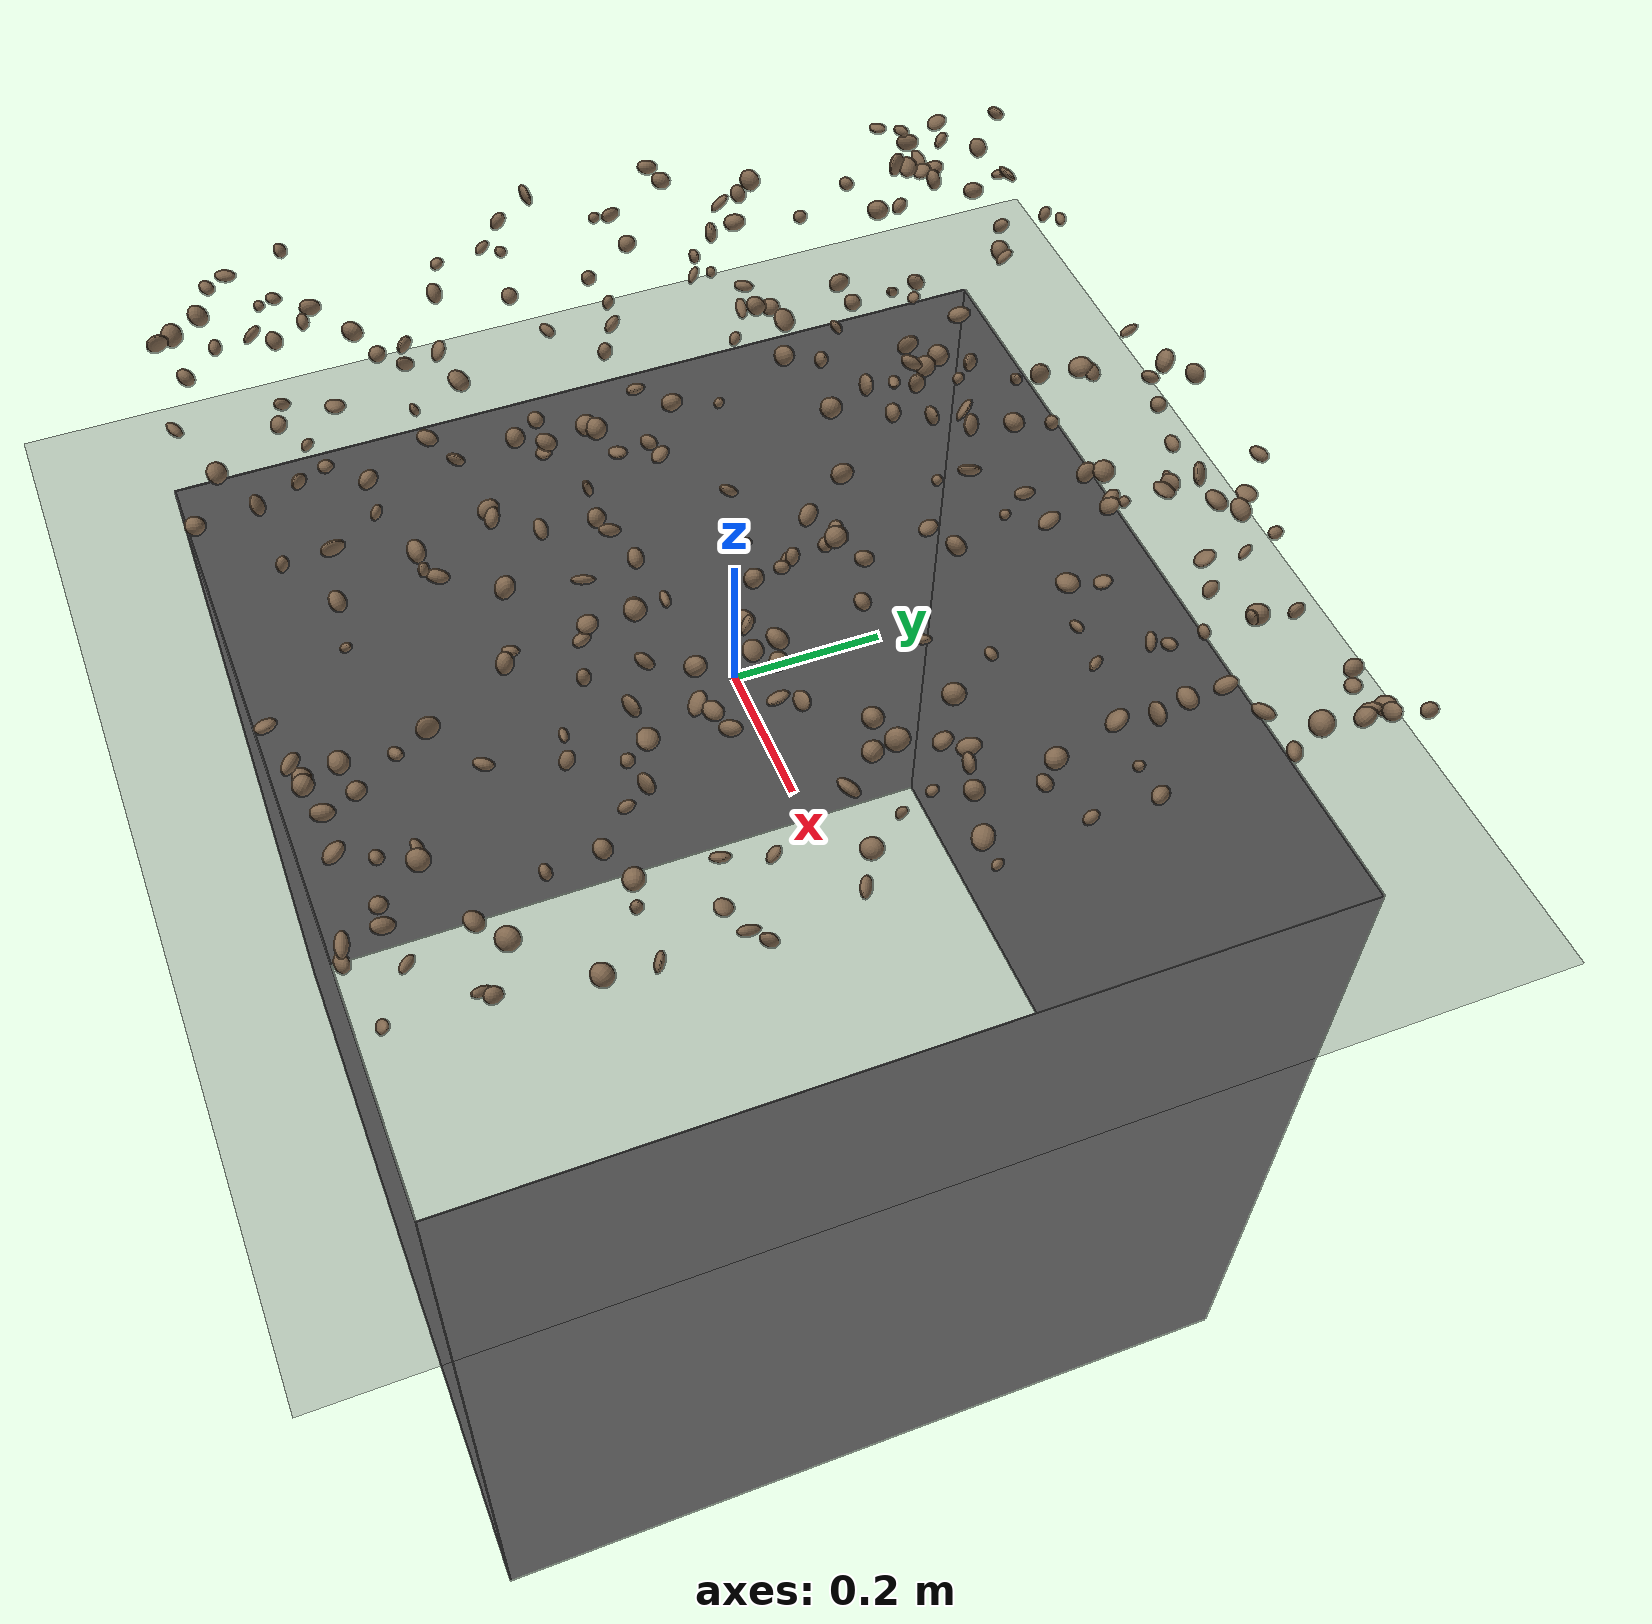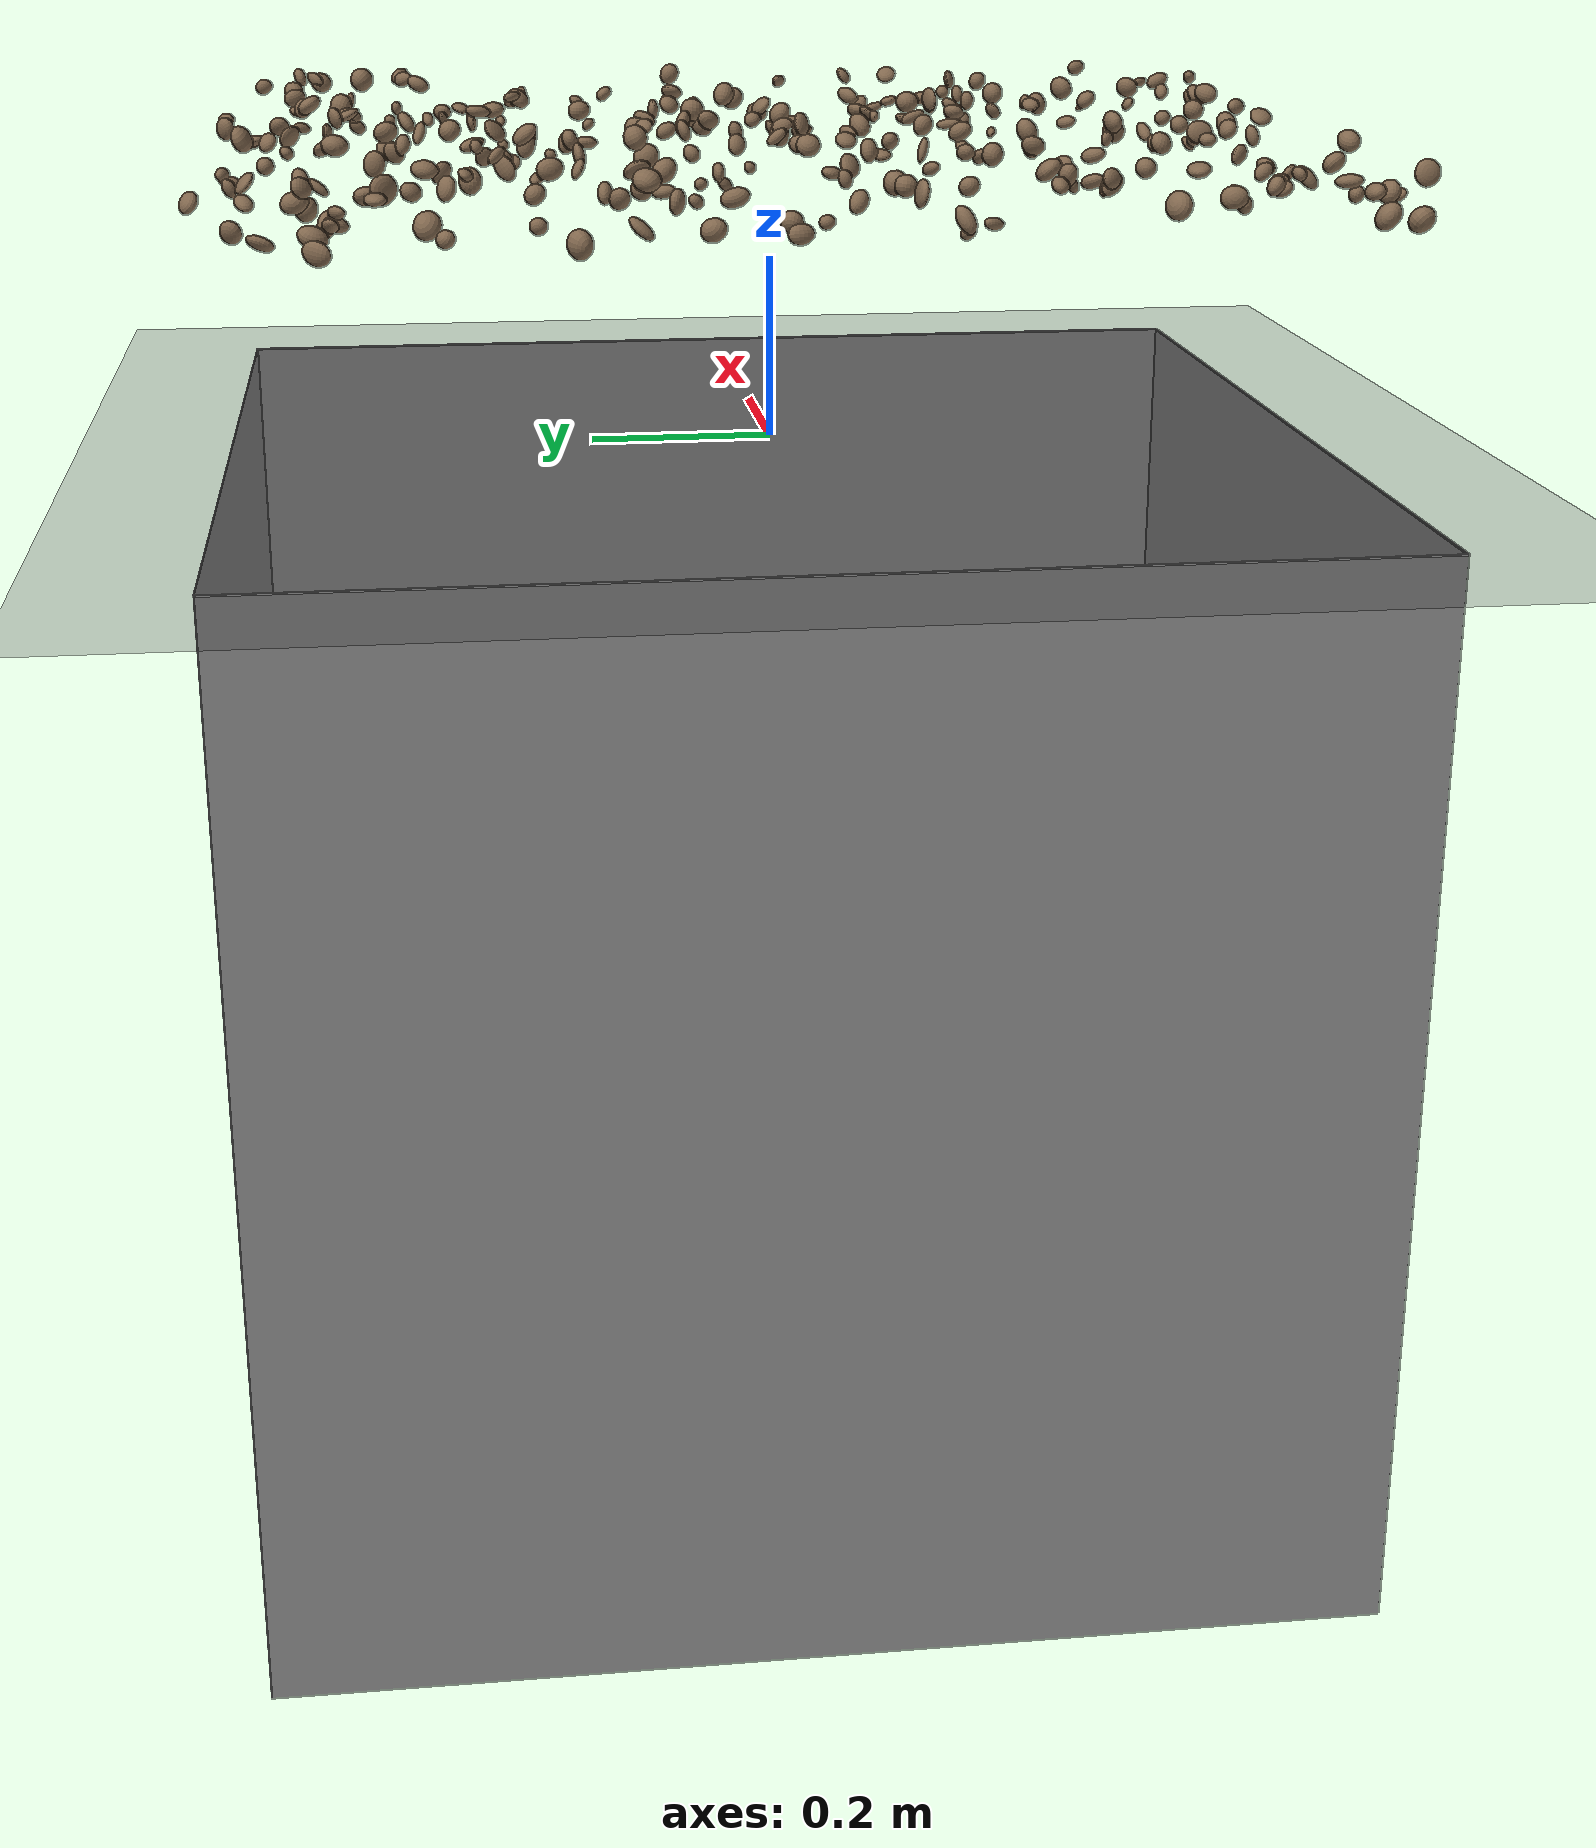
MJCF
<mujoco model="rocky_terrain_scene">
    <compiler angle="radian" inertiafromgeom="true" />
    <option timestep="0.002" gravity="0 0 -9.81" />

    <worldbody>
        <light name="sunlight" pos="5 5 5" dir="-1 -1 -1" diffuse="1 1 1" specular="0.5 0.5 0.5" ambient="0.5 0.5 0.5" />

        <geom name="ground_plane" type="plane" size="50 50 0.1" rgba="0.3 0.3 0.3 1" />

        <body name="rocky_terrain_body">

        </body>
    <body name="rock1" pos="-0.4369631453269402 -0.03208340025546563 0.3195802045404572"><joint type="free" /><geom type="ellipsoid" size="0.009083993362357828 0.012958761064077642 0.008740674688470718" quat="0.08619168053215329 0.3676581646751083 0.2752281464645867 0.27092200832815166" rgba="0.5 0.4 0.3 1" /><inertial pos="-0.4369631453269402 -0.03208340025546563 0.3195802045404572" quat="0.08619168053215329 0.3676581646751083 0.2752281464645867 0.27092200832815166" mass="1.5263077938780415e-05" /></body><body name="rock2" pos="-0.06932443006903533 -0.46185788129742267 0.33737150139833283"><joint type="free" /><geom type="ellipsoid" size="0.014855624154948295 0.01228357068436943 0.005377363947391852" quat="0.21324567825190677 0.2610580568367049 0.27912862264092997 0.24656764227045838" rgba="0.5 0.4 0.3 1" /><inertial pos="-0.06932443006903533 -0.46185788129742267 0.33737150139833283" quat="0.21324567825190677 0.2610580568367049 0.27912862264092997 0.24656764227045838" mass="7.878507683898176e-05" /></body><body name="rock3" pos="-0.18687673626561757 -0.056369489419285324 0.3476233491591556"><joint type="free" /><geom type="ellipsoid" size="0.010326804325229432 0.011089583266283384 0.006356837078295076" quat="0.20330341498013504 0.13401094778498415 0.6066529592938821 0.056032677940998775" rgba="0.5 0.4 0.3 1" /><inertial pos="-0.18687673626561757 -0.056369489419285324 0.3476233491591556" quat="0.20330341498013504 0.13401094778498415 0.6066529592938821 0.056032677940998775" mass="9.461220480885216e-05" /></body><body name="rock4" pos="0.3467346582497335 -0.5715172523903669 0.33348093493587244"><joint type="free" /><geom type="ellipsoid" size="0.014667571528533284 0.008416460304547508 0.013748670631210404" quat="0.2624287294440301 0.3585329003911277 0.03649454135967227 0.34254382880516987" rgba="0.5 0.4 0.3 1" /><inertial pos="0.3467346582497335 -0.5715172523903669 0.33348093493587244" quat="0.2624287294440301 0.3585329003911277 0.03649454135967227 0.34254382880516987" mass="1.1258999602248254e-05" /></body><body name="rock5" pos="0.18130258665227894 0.39312790764308014 0.3317273987820918"><joint type="free" /><geom type="ellipsoid" size="0.007759269958888745 0.010256497027308863 0.013879615070932546" quat="0.4036409673178775 0.015245064999816225 0.24191981581461258 0.3391941518676937" rgba="0.5 0.4 0.3 1" /><inertial pos="0.18130258665227894 0.39312790764308014 0.3317273987820918" quat="0.4036409673178775 0.015245064999816225 0.24191981581461258 0.3391941518676937" mass="4.2724544233898134e-05" /></body><body name="rock6" pos="0.4667998095182918 -0.5934326682843681 0.3434987891097414"><joint type="free" /><geom type="ellipsoid" size="0.0075388753553394345 0.007506246908369034 0.014432108946847082" quat="0.23284733688480805 0.3507371154268103 0.22054740050471255 0.19586814718366902" rgba="0.5 0.4 0.3 1" /><inertial pos="0.4667998095182918 -0.5934326682843681 0.3434987891097414" quat="0.23284733688480805 0.3507371154268103 0.22054740050471255 0.19586814718366902" mass="5.292989842185913e-05" /></body><body name="rock7" pos="0.46715793231797653 -0.29132287356248115 0.30402053074821583"><joint type="free" /><geom type="ellipsoid" size="0.011867464427159594 0.012758761834892027 0.012934097489568364" quat="0.37551001265122785 0.18797115704406084 0.3539204152336489 0.0825984150710624" rgba="0.5 0.4 0.3 1" /><inertial pos="0.46715793231797653 -0.29132287356248115 0.30402053074821583" quat="0.37551001265122785 0.18797115704406084 0.3539204152336489 0.0825984150710624" mass="1.5938911117883663e-05" /></body><body name="rock8" pos="0.4449440261477352 -0.04335507258911031 0.31651644399029194"><joint type="free" /><geom type="ellipsoid" size="0.006997873995780226 0.012770035866640814 0.014821847108061871" quat="0.01936538110967175 0.3382506903040711 0.32911458617490824 0.3132693424113488" rgba="0.5 0.4 0.3 1" /><inertial pos="0.4449440261477352 -0.04335507258911031 0.31651644399029194" quat="0.01936538110967175 0.3382506903040711 0.32911458617490824 0.3132693424113488" mass="5.1972323933262094e-05" /></body><body name="rock9" pos="-0.4336926418071867 -0.5531105214699223 0.32024248978254727"><joint type="free" /><geom type="ellipsoid" size="0.009284464475405709 0.012013746006048374 0.012250061154495596" quat="0.2745876297852432 0.17787617390700006 0.05435415742057474 0.49318203888718204" rgba="0.5 0.4 0.3 1" /><inertial pos="-0.4336926418071867 -0.5531105214699223 0.32024248978254727" quat="0.2745876297852432 0.17787617390700006 0.05435415742057474 0.49318203888718204" mass="2.3511487048804146e-05" /></body><body name="rock10" pos="-0.3389166093234591 -0.11834113378439082 0.33682547499257887"><joint type="free" /><geom type="ellipsoid" size="0.006774159400278323 0.006557281443120484 0.010665672443748667" quat="0.06798358347154504 0.30200643522776577 0.3289391991406414 0.30107078216004773" rgba="0.5 0.4 0.3 1" /><inertial pos="-0.3389166093234591 -0.11834113378439082 0.33682547499257887" quat="0.06798358347154504 0.30200643522776577 0.3289391991406414 0.30107078216004773" mass="1.8326113292060253e-05" /></body><body name="rock11" pos="-0.36391347068431745 -0.25236636453414896 0.32552798781887776"><joint type="free" /><geom type="ellipsoid" size="0.006585182293347302 0.01302491052219774 0.013217461811490656" quat="0.3646331580042316 0.1284724756982111 0.28623944579144484 0.22065492050611255" rgba="0.5 0.4 0.3 1" /><inertial pos="-0.36391347068431745 -0.25236636453414896 0.32552798781887776" quat="0.3646331580042316 0.1284724756982111 0.28623944579144484 0.22065492050611255" mass="8.862466555880621e-05" /></body><body name="rock12" pos="0.02538214245231596 -0.1623584496130518 0.3467018302919097"><joint type="free" /><geom type="ellipsoid" size="0.014050675303472034 0.007076984530908555 0.005828774315401265" quat="0.3718170065149457 0.10004680907444943 0.22945837421212517 0.2986778101984798" rgba="0.5 0.4 0.3 1" /><inertial pos="0.02538214245231596 -0.1623584496130518 0.3467018302919097" quat="0.3718170065149457 0.10004680907444943 0.22945837421212517 0.2986778101984798" mass="5.1266519948426626e-05" /></body><body name="rock13" pos="-0.5688976239539499 -0.46722869543258816 0.3489964188695622"><joint type="free" /><geom type="ellipsoid" size="0.013340120559215029 0.006612456116632642 0.009012019418181295" quat="0.3017045550000533 0.2704689900684336 0.2214686559357824 0.20635779899573073" rgba="0.5 0.4 0.3 1" /><inertial pos="-0.5688976239539499 -0.46722869543258816 0.3489964188695622" quat="0.3017045550000533 0.2704689900684336 0.2214686559357824 0.20635779899573073" mass="3.348676845891388e-05" /></body><body name="rock14" pos="0.3223216203493926 -0.223229665995687 0.3364928121470451"><joint type="free" /><geom type="ellipsoid" size="0.012446836572137366 0.0077982993389415665 0.014108716700535318" quat="0.3044558156392406 0.29969349604575046 0.2267965805414685 0.16905410777354046" rgba="0.5 0.4 0.3 1" /><inertial pos="0.3223216203493926 -0.223229665995687 0.3364928121470451" quat="0.3044558156392406 0.29969349604575046 0.2267965805414685 0.16905410777354046" mass="2.222391431453906e-05" /></body><body name="rock15" pos="-0.36067041449166476 -0.2961349569811554 0.3210959667684651"><joint type="free" /><geom type="ellipsoid" size="0.009158955579243518 0.012994916762576737 0.005149676577396435" quat="0.10872883982982869 0.35166623144310555 0.1706980720912447 0.36890685663582096" rgba="0.5 0.4 0.3 1" /><inertial pos="-0.36067041449166476 -0.2961349569811554 0.3210959667684651" quat="0.10872883982982869 0.35166623144310555 0.1706980720912447 0.36890685663582096" mass="3.583651567482081e-05" /></body><body name="rock16" pos="-0.4138662616096506 0.3894393768941784 0.3323791924573324"><joint type="free" /><geom type="ellipsoid" size="0.011082962686728249 0.009252772410331601 0.008521278044848745" quat="0.06943107334494603 0.2787073289537909 0.3671160464526874 0.28474555124857576" rgba="0.5 0.4 0.3 1" /><inertial pos="-0.4138662616096506 0.3894393768941784 0.3323791924573324" quat="0.06943107334494603 0.2787073289537909 0.3671160464526874 0.28474555124857576" mass="4.358965529582343e-05" /></body><body name="rock17" pos="-0.18584797374007533 -0.10893365916712577 0.3032737430762318"><joint type="free" /><geom type="ellipsoid" size="0.012730647420901913 0.013471989742705689 0.013435217311419011" quat="0.27278917381478257 0.14270349959395373 0.260437095264405 0.32407023132685864" rgba="0.5 0.4 0.3 1" /><inertial pos="-0.18584797374007533 -0.10893365916712577 0.3032737430762318" quat="0.27278917381478257 0.14270349959395373 0.260437095264405 0.32407023132685864" mass="5.903548481736629e-05" /></body><body name="rock18" pos="0.39721650488208016 0.2661877318132343 0.3369385203360556"><joint type="free" /><geom type="ellipsoid" size="0.012365852437161193 0.005698796205669855 0.0054353422400868516" quat="0.20341826130042448 0.12466062389844089 0.3261972154002178 0.34572389940091686" rgba="0.5 0.4 0.3 1" /><inertial pos="0.39721650488208016 0.2661877318132343 0.3369385203360556" quat="0.20341826130042448 0.12466062389844089 0.3261972154002178 0.34572389940091686" mass="5.219564200231153e-05" /></body><body name="rock19" pos="-0.5061896146442357 -0.21070175268236319 0.34121146204227765"><joint type="free" /><geom type="ellipsoid" size="0.00873572464832877 0.006886450066125162 0.010568305457137085" quat="0.26282552666548337 0.24929658165594626 0.1379751359008088 0.3499027557777615" rgba="0.5 0.4 0.3 1" /><inertial pos="-0.5061896146442357 -0.21070175268236319 0.34121146204227765" quat="0.26282552666548337 0.24929658165594626 0.1379751359008088 0.3499027557777615" mass="3.1477140535382326e-05" /></body><body name="rock20" pos="-0.5929040852907593 -0.39067415095865143 0.3489513643492934"><joint type="free" /><geom type="ellipsoid" size="0.007359044768727651 0.009513030403314679 0.010779929391215127" quat="0.348266014391645 0.264987738814142 0.0333282755390016 0.3534179712552114" rgba="0.5 0.4 0.3 1" /><inertial pos="-0.5929040852907593 -0.39067415095865143 0.3489513643492934" quat="0.348266014391645 0.264987738814142 0.0333282755390016 0.3534179712552114" mass="2.5922828608755862e-05" /></body><body name="rock21" pos="-0.28140175921812455 0.10808752872416139 0.30098705624277694"><joint type="free" /><geom type="ellipsoid" size="0.006758406875667296 0.007003155992558968 0.0089066301939796" quat="0.26020854054952713 0.4361675229342349 0.2734023235111413 0.030221613005096674" rgba="0.5 0.4 0.3 1" /><inertial pos="-0.28140175921812455 0.10808752872416139 0.30098705624277694" quat="0.26020854054952713 0.4361675229342349 0.2734023235111413 0.030221613005096674" mass="1.9196031972330098e-05" /></body><body name="rock22" pos="0.41804798568170753 -0.005427874920047038 0.32947203311922313"><joint type="free" /><geom type="ellipsoid" size="0.011971165099572504 0.014034253813678736 0.011452345438971393" quat="0.008660746823739044 0.3702207808886716 0.2456443595288861 0.37547411275870324" rgba="0.5 0.4 0.3 1" /><inertial pos="0.41804798568170753 -0.005427874920047038 0.32947203311922313" quat="0.008660746823739044 0.3702207808886716 0.2456443595288861 0.37547411275870324" mass="6.511832993287576e-05" /></body><body name="rock23" pos="-0.32727371676284456 0.49453238388968856 0.3336760293336569"><joint type="free" /><geom type="ellipsoid" size="0.008043680375328276 0.008233439897789102 0.013368283322918773" quat="0.4066095088311034 0.0648936770732103 0.1937928893246854 0.33470392477100086" rgba="0.5 0.4 0.3 1" /><inertial pos="-0.32727371676284456 0.49453238388968856 0.3336760293336569" quat="0.4066095088311034 0.0648936770732103 0.1937928893246854 0.33470392477100086" mass="9.567701461479249e-05" /></body><body name="rock24" pos="0.23380422544004553 0.5381475902468406 0.32273540423123737"><joint type="free" /><geom type="ellipsoid" size="0.011329027641656516 0.008661263247780984 0.014317625164454024" quat="0.10077678375967193 0.34547561772437535 0.33453396774783534 0.21921363076811737" rgba="0.5 0.4 0.3 1" /><inertial pos="0.23380422544004553 0.5381475902468406 0.32273540423123737" quat="0.10077678375967193 0.34547561772437535 0.33453396774783534 0.21921363076811737" mass="4.3964599881141954e-05" /></body><body name="rock25" pos="0.09395015119582228 0.07670341762099298 0.3025919457965265"><joint type="free" /><geom type="ellipsoid" size="0.010660007601148602 0.008868112247049535 0.008553824602605176" quat="0.23532526131732215 0.3944621210672031 0.039284488264741076 0.3309281293507337" rgba="0.5 0.4 0.3 1" /><inertial pos="0.09395015119582228 0.07670341762099298 0.3025919457965265" quat="0.23532526131732215 0.3944621210672031 0.039284488264741076 0.3309281293507337" mass="2.9023340419502432e-05" /></body><body name="rock26" pos="-0.5853538003989515 -0.10693378612928972 0.32240358384947865"><joint type="free" /><geom type="ellipsoid" size="0.014448455216904483 0.008271686110959822 0.008208568674929391" quat="0.20479293037390522 0.4305378883047285 0.018060490091600368 0.3466086912297659" rgba="0.5 0.4 0.3 1" /><inertial pos="-0.5853538003989515 -0.10693378612928972 0.32240358384947865" quat="0.20479293037390522 0.4305378883047285 0.018060490091600368 0.3466086912297659" mass="5.789861962820433e-05" /></body><body name="rock27" pos="0.5199916436469828 0.14655934142304916 0.32654338655584464"><joint type="free" /><geom type="ellipsoid" size="0.007412699707030257 0.010782700210260258 0.010291636666792291" quat="0.038258807781433736 0.4300224591222528 0.2186217774954447 0.3130969556008688" rgba="0.5 0.4 0.3 1" /><inertial pos="0.5199916436469828 0.14655934142304916 0.32654338655584464" quat="0.038258807781433736 0.4300224591222528 0.2186217774954447 0.3130969556008688" mass="9.396969039629093e-05" /></body><body name="rock28" pos="-0.0167546914505472 0.3105923500212481 0.3156732467441923"><joint type="free" /><geom type="ellipsoid" size="0.01045192338890872 0.012946299948856835 0.005703542126919137" quat="0.3560665664548196 0.078025574709892 0.25059756867103467 0.3153102901642537" rgba="0.5 0.4 0.3 1" /><inertial pos="-0.0167546914505472 0.3105923500212481 0.3156732467441923" quat="0.3560665664548196 0.078025574709892 0.25059756867103467 0.3153102901642537" mass="4.697248180227671e-05" /></body><body name="rock29" pos="0.5596850507556529 0.057442448950256075 0.323764325405553"><joint type="free" /><geom type="ellipsoid" size="0.014119893319863266 0.008070127803195274 0.01228189233646576" quat="0.02460295877503185 0.22115340712456458 0.36176529925711176 0.3924783348432918" rgba="0.5 0.4 0.3 1" /><inertial pos="0.5596850507556529 0.057442448950256075 0.323764325405553" quat="0.02460295877503185 0.22115340712456458 0.36176529925711176 0.3924783348432918" mass="3.582387567540209e-05" /></body><body name="rock30" pos="-0.07251054925029488 -0.15699323996347359 0.3224465992618965"><joint type="free" /><geom type="ellipsoid" size="0.005141425630350742 0.014028582355146531 0.006702993453375975" quat="0.20020550338391843 0.29810757754673695 0.24201340750477615 0.25967351156456847" rgba="0.5 0.4 0.3 1" /><inertial pos="-0.07251054925029488 -0.15699323996347359 0.3224465992618965" quat="0.20020550338391843 0.29810757754673695 0.24201340750477615 0.25967351156456847" mass="7.090892173562438e-05" /></body><body name="rock31" pos="-0.4480433232273767 -0.4372887107986418 0.33116835195587707"><joint type="free" /><geom type="ellipsoid" size="0.011747942886047642 0.010008436178046788 0.008628148528717246" quat="0.5748500040346656 0.009320428470096436 0.2715852506476341 0.14424431684760375" rgba="0.5 0.4 0.3 1" /><inertial pos="-0.4480433232273767 -0.4372887107986418 0.33116835195587707" quat="0.5748500040346656 0.009320428470096436 0.2715852506476341 0.14424431684760375" mass="8.569106572977705e-05" /></body><body name="rock32" pos="0.5744298756770149 -0.36159083242454126 0.3155280524654102"><joint type="free" /><geom type="ellipsoid" size="0.013318946875270733 0.01367305731840782 0.012094160914651006" quat="0.36901914733815394 0.38524559615020765 0.09042211589443738 0.155313140617201" rgba="0.5 0.4 0.3 1" /><inertial pos="0.5744298756770149 -0.36159083242454126 0.3155280524654102" quat="0.36901914733815394 0.38524559615020765 0.09042211589443738 0.155313140617201" mass="3.3380167898564744e-05" /></body><body name="rock33" pos="0.3909033109326495 -0.4940214053845404 0.3393359409571132"><joint type="free" /><geom type="ellipsoid" size="0.013103213161782638 0.012790739219101111 0.009773878708623203" quat="0.3336481487714176 0.26758344057539135 0.08671340241049079 0.31205500824270027" rgba="0.5 0.4 0.3 1" /><inertial pos="0.3909033109326495 -0.4940214053845404 0.3393359409571132" quat="0.3336481487714176 0.26758344057539135 0.08671340241049079 0.31205500824270027" mass="6.046361897311668e-05" /></body><body name="rock34" pos="-0.28315817249750214 0.4798101645793472 0.32089480927213476"><joint type="free" /><geom type="ellipsoid" size="0.01235923710068276 0.005167206672663162 0.0069035179642035534" quat="0.17142769599849406 0.34827018271989685 0.14949006785827554 0.33081205342333353" rgba="0.5 0.4 0.3 1" /><inertial pos="-0.28315817249750214 0.4798101645793472 0.32089480927213476" quat="0.17142769599849406 0.34827018271989685 0.14949006785827554 0.33081205342333353" mass="5.5274080844134724e-05" /></body><body name="rock35" pos="0.16083886749770515 0.5240245891555398 0.31946877123962164"><joint type="free" /><geom type="ellipsoid" size="0.014887406498503574 0.013427923325242508 0.006403669851524409" quat="0.11933128274672583 0.12539463222947395 0.2872707186247971 0.46800336639900303" rgba="0.5 0.4 0.3 1" /><inertial pos="0.16083886749770515 0.5240245891555398 0.31946877123962164" quat="0.11933128274672583 0.12539463222947395 0.2872707186247971 0.46800336639900303" mass="3.50097365400569e-05" /></body><body name="rock36" pos="-0.17704762001582386 -0.2122598598420412 0.32981712271710456"><joint type="free" /><geom type="ellipsoid" size="0.011387945854175602 0.012426170511397957 0.011025068026142079" quat="0.1905597648322642 0.15837372423986645 0.30918578412051095 0.3418807268073585" rgba="0.5 0.4 0.3 1" /><inertial pos="-0.17704762001582386 -0.2122598598420412 0.32981712271710456" quat="0.1905597648322642 0.15837372423986645 0.30918578412051095 0.3418807268073585" mass="7.606211977420235e-05" /></body><body name="rock37" pos="0.12181519542058628 0.1927462785431049 0.3130765189767847"><joint type="free" /><geom type="ellipsoid" size="0.009550868651824633 0.007031467693877557 0.012576554061056473" quat="0.41504299507557146 0.4444015060550026 0.11017549209743699 0.03038000677198903" rgba="0.5 0.4 0.3 1" /><inertial pos="0.12181519542058628 0.1927462785431049 0.3130765189767847" quat="0.41504299507557146 0.4444015060550026 0.11017549209743699 0.03038000677198903" mass="6.883401024104622e-05" /></body><body name="rock38" pos="0.39075093172457265 0.4711442131672082 0.32883976204239895"><joint type="free" /><geom type="ellipsoid" size="0.011593822014957848 0.014710571372309321 0.013230807952153829" quat="0.053343581882867974 0.14059628085180434 0.3472089106125992 0.4588512266527286" rgba="0.5 0.4 0.3 1" /><inertial pos="0.39075093172457265 0.4711442131672082 0.32883976204239895" quat="0.053343581882867974 0.14059628085180434 0.3472089106125992 0.4588512266527286" mass="6.667148993427567e-05" /></body><body name="rock39" pos="-0.3700139310062952 -0.32640320878051227 0.33829101161975966"><joint type="free" /><geom type="ellipsoid" size="0.010540840425213981 0.009891185221230716 0.010341863928902894" quat="0.27050900543489087 0.2730227021012535 0.17219896364104198 0.2842693288228137" rgba="0.5 0.4 0.3 1" /><inertial pos="-0.3700139310062952 -0.32640320878051227 0.33829101161975966" quat="0.27050900543489087 0.2730227021012535 0.17219896364104198 0.2842693288228137" mass="6.619729867583304e-05" /></body><body name="rock40" pos="0.39024261463324916 0.4048403117878435 0.3255884226498344"><joint type="free" /><geom type="ellipsoid" size="0.006021021287638879 0.009024373914693948 0.007587885842906607" quat="0.333902534560325 0.11750440519074398 0.16373143410823435 0.3848616261406967" rgba="0.5 0.4 0.3 1" /><inertial pos="0.39024261463324916 0.4048403117878435 0.3255884226498344" quat="0.333902534560325 0.11750440519074398 0.16373143410823435 0.3848616261406967" mass="3.8030569848030356e-05" /></body><body name="rock41" pos="0.2757386552326503 0.2928426291104562 0.33402702989620336"><joint type="free" /><geom type="ellipsoid" size="0.01387005157411193 0.009254785980978252 0.013415454913571389" quat="0.3647256327258786 0.30752951596750644 0.1614523712752834 0.16629248003133168" rgba="0.5 0.4 0.3 1" /><inertial pos="0.2757386552326503 0.2928426291104562 0.33402702989620336" quat="0.3647256327258786 0.30752951596750644 0.1614523712752834 0.16629248003133168" mass="7.844137860306974e-05" /></body><body name="rock42" pos="0.58869204252816 0.40076326555511466 0.34468248159832804"><joint type="free" /><geom type="ellipsoid" size="0.010060862008060573 0.00805268156837861 0.014049997730995939" quat="0.4787819504382611 0.20168924727740614 0.3107156903523191 0.008813111932013708" rgba="0.5 0.4 0.3 1" /><inertial pos="0.58869204252816 0.40076326555511466 0.34468248159832804" quat="0.4787819504382611 0.20168924727740614 0.3107156903523191 0.008813111932013708" mass="7.04701677001789e-05" /></body><body name="rock43" pos="-0.4487619435073682 0.375458512552722 0.30564164524749804"><joint type="free" /><geom type="ellipsoid" size="0.014037236433254652 0.014773504421002188 0.011847426834757075" quat="0.22417898002839123 0.3968258402931959 0.2813886084080716 0.09760657127034122" rgba="0.5 0.4 0.3 1" /><inertial pos="-0.4487619435073682 0.375458512552722 0.30564164524749804" quat="0.22417898002839123 0.3968258402931959 0.2813886084080716 0.09760657127034122" mass="7.330113813509758e-05" /></body><body name="rock44" pos="0.2894871112058708 0.32947594501047595 0.335011026249211"><joint type="free" /><geom type="ellipsoid" size="0.0104151125991435 0.005363847976575258 0.010884278784761066" quat="0.19495027562901185 0.1653905537047953 0.25697384374511184 0.38268532692108104" rgba="0.5 0.4 0.3 1" /><inertial pos="0.2894871112058708 0.32947594501047595 0.335011026249211" quat="0.19495027562901185 0.1653905537047953 0.25697384374511184 0.38268532692108104" mass="4.216623352683013e-05" /></body><body name="rock45" pos="-0.01342831777208775 -0.3583100067498267 0.3073821596334826"><joint type="free" /><geom type="ellipsoid" size="0.013809541621746281 0.009280721753683826 0.008031310895562593" quat="0.1605619259817215 0.4745103099505364 0.339814120652335 0.025113643415407075" rgba="0.5 0.4 0.3 1" /><inertial pos="-0.01342831777208775 -0.3583100067498267 0.3073821596334826" quat="0.1605619259817215 0.4745103099505364 0.339814120652335 0.025113643415407075" mass="2.6805554290257856e-05" /></body><body name="rock46" pos="-0.38450133013789184 -0.2893256399597548 0.33058518733611636"><joint type="free" /><geom type="ellipsoid" size="0.012327816665459936 0.010294076930700419 0.0061525401928458475" quat="0.1417371152515546 0.18673206216139887 0.3524418529285766 0.31908896965846995" rgba="0.5 0.4 0.3 1" /><inertial pos="-0.38450133013789184 -0.2893256399597548 0.33058518733611636" quat="0.1417371152515546 0.18673206216139887 0.3524418529285766 0.31908896965846995" mass="8.937485033459759e-05" /></body><body name="rock47" pos="-0.28152788602936235 0.35517706740289523 0.3176791310601459"><joint type="free" /><geom type="ellipsoid" size="0.010929120091883994 0.013341861050019083 0.007181675829284816" quat="0.2964862787317019 0.3984661912936854 0.17960973365496893 0.12543779631964375" rgba="0.5 0.4 0.3 1" /><inertial pos="-0.28152788602936235 0.35517706740289523 0.3176791310601459" quat="0.2964862787317019 0.3984661912936854 0.17960973365496893 0.12543779631964375" mass="7.29232647179906e-05" /></body><body name="rock48" pos="0.28376269320021463 -0.15322243456620788 0.3226112404743505"><joint type="free" /><geom type="ellipsoid" size="0.014474382408583623 0.005818893005268954 0.010761561131668995" quat="0.07211082742888092 0.25943750437138596 0.2334626316882474 0.4349890365114857" rgba="0.5 0.4 0.3 1" /><inertial pos="0.28376269320021463 -0.15322243456620788 0.3226112404743505" quat="0.07211082742888092 0.25943750437138596 0.2334626316882474 0.4349890365114857" mass="5.239284145888378e-05" /></body><body name="rock49" pos="0.0008708332879836522 0.5404864106924455 0.33198218522223527"><joint type="free" /><geom type="ellipsoid" size="0.010918962181101773 0.0067782863536900405 0.011273930124888788" quat="0.4576410908334165 0.07672804520182167 0.22438017517347503 0.2412506887912868" rgba="0.5 0.4 0.3 1" /><inertial pos="0.0008708332879836522 0.5404864106924455 0.33198218522223527" quat="0.4576410908334165 0.07672804520182167 0.22438017517347503 0.2412506887912868" mass="6.440226519515164e-05" /></body><body name="rock50" pos="-0.2441266540054136 0.3043396312446137 0.34473079057455047"><joint type="free" /><geom type="ellipsoid" size="0.006003420808541106 0.011314444592712455 0.005329205163124934" quat="0.008689506976360598 0.30706840949414155 0.24177240632132982 0.442469677208168" rgba="0.5 0.4 0.3 1" /><inertial pos="-0.2441266540054136 0.3043396312446137 0.34473079057455047" quat="0.008689506976360598 0.30706840949414155 0.24177240632132982 0.442469677208168" mass="9.90105100127287e-05" /></body><body name="rock51" pos="0.5057306107503717 -0.5393482376161088 0.3342854477704144"><joint type="free" /><geom type="ellipsoid" size="0.012046279983884831 0.006268816439882795 0.005361465276172827" quat="0.19298021596222228 0.11616745703406584 0.2720715541405004 0.41878077286321147" rgba="0.5 0.4 0.3 1" /><inertial pos="0.5057306107503717 -0.5393482376161088 0.3342854477704144" quat="0.19298021596222228 0.11616745703406584 0.2720715541405004 0.41878077286321147" mass="5.6186646598093265e-05" /></body><body name="rock52" pos="0.021316924059077147 0.3466390049536854 0.33969672663821243"><joint type="free" /><geom type="ellipsoid" size="0.012571670598309992 0.01165025300239789 0.010767617594734174" quat="0.287178030845766 0.4029274625121033 0.2808812640067143 0.029013242635416416" rgba="0.5 0.4 0.3 1" /><inertial pos="0.021316924059077147 0.3466390049536854 0.33969672663821243" quat="0.287178030845766 0.4029274625121033 0.2808812640067143 0.029013242635416416" mass="7.813611979413926e-05" /></body><body name="rock53" pos="0.570946695874654 0.25785810226303363 0.3158220624926428"><joint type="free" /><geom type="ellipsoid" size="0.014882342897260106 0.009354964364776171 0.008976118173320315" quat="0.20705025931525445 0.12908638862649496 0.40927259671311184 0.2545907553451388" rgba="0.5 0.4 0.3 1" /><inertial pos="0.570946695874654 0.25785810226303363 0.3158220624926428" quat="0.20705025931525445 0.12908638862649496 0.40927259671311184 0.2545907553451388" mass="3.0319458170663693e-05" /></body><body name="rock54" pos="0.27748486846284637 0.11573415661826769 0.31258084858347435"><joint type="free" /><geom type="ellipsoid" size="0.010532777652116833 0.005658844886467648 0.011387363509842003" quat="0.3819333729735613 0.1078096226789204 0.20491109130765991 0.3053459130398585" rgba="0.5 0.4 0.3 1" /><inertial pos="0.27748486846284637 0.11573415661826769 0.31258084858347435" quat="0.3819333729735613 0.1078096226789204 0.20491109130765991 0.3053459130398585" mass="1.827533408487389e-05" /></body><body name="rock55" pos="-0.0039872990326126345 -0.16866530551467418 0.34143468182957903"><joint type="free" /><geom type="ellipsoid" size="0.011139111345609388 0.012012210114706417 0.009792217757437396" quat="0.07305937537856987 0.23014436736391022 0.25444556052076533 0.44235069673675453" rgba="0.5 0.4 0.3 1" /><inertial pos="-0.0039872990326126345 -0.16866530551467418 0.34143468182957903" quat="0.07305937537856987 0.23014436736391022 0.25444556052076533 0.44235069673675453" mass="8.010969064636328e-05" /></body><body name="rock56" pos="0.09983674065168724 0.4077554365679191 0.3074697235740855"><joint type="free" /><geom type="ellipsoid" size="0.013317197386886692 0.010951835498033205 0.007316874615981585" quat="0.16125210447389943 0.33351320839529497 0.062303741660818486 0.4429309454699871" rgba="0.5 0.4 0.3 1" /><inertial pos="0.09983674065168724 0.4077554365679191 0.3074697235740855" quat="0.16125210447389943 0.33351320839529497 0.062303741660818486 0.4429309454699871" mass="2.215565393869411e-05" /></body><body name="rock57" pos="0.08513841283413082 -0.024663963231819075 0.3326456165377035"><joint type="free" /><geom type="ellipsoid" size="0.005888594200974817 0.011936326777048787 0.008726245816580658" quat="0.025746442118821457 0.11948194530074666 0.13261677541295874 0.7221548371674731" rgba="0.5 0.4 0.3 1" /><inertial pos="0.08513841283413082 -0.024663963231819075 0.3326456165377035" quat="0.025746442118821457 0.11948194530074666 0.13261677541295874 0.7221548371674731" mass="2.132450391877137e-05" /></body><body name="rock58" pos="-0.12942324900368263 0.2592681378559055 0.30669653097152944"><joint type="free" /><geom type="ellipsoid" size="0.013935495770797331 0.005133459563348474 0.00707865331922692" quat="0.12752435321491448 0.012671387539031248 0.4360852360391681 0.4237190232068862" rgba="0.5 0.4 0.3 1" /><inertial pos="-0.12942324900368263 0.2592681378559055 0.30669653097152944" quat="0.12752435321491448 0.012671387539031248 0.4360852360391681 0.4237190232068862" mass="4.567218395016549e-05" /></body><body name="rock59" pos="0.021917617005737244 0.5456128298097483 0.30454989410714317"><joint type="free" /><geom type="ellipsoid" size="0.009587095145738975 0.009588968448509535 0.009820889028181781" quat="0.30600904576268456 0.11492550856218424 0.284669971446962 0.29439547422816914" rgba="0.5 0.4 0.3 1" /><inertial pos="0.021917617005737244 0.5456128298097483 0.30454989410714317" quat="0.30600904576268456 0.11492550856218424 0.284669971446962 0.29439547422816914" mass="8.993627724723982e-05" /></body><body name="rock60" pos="-0.044861687614563106 0.4686020154684808 0.33312778397554216"><joint type="free" /><geom type="ellipsoid" size="0.014946701789531964 0.011420198048958358 0.013498021517626326" quat="0.2681510230468339 0.2982376720004634 0.2041329683845364 0.22947833656816632" rgba="0.5 0.4 0.3 1" /><inertial pos="-0.044861687614563106 0.4686020154684808 0.33312778397554216" quat="0.2681510230468339 0.2982376720004634 0.2041329683845364 0.22947833656816632" mass="6.183100856050164e-05" /></body><body name="rock61" pos="-0.19785975290372726 -0.11799960276495014 0.30180375444096763"><joint type="free" /><geom type="ellipsoid" size="0.012481207917526865 0.013082546043608832 0.011781266318455722" quat="0.5978062050401984 0.07771261633142434 0.048376165310523904 0.2761050133178534" rgba="0.5 0.4 0.3 1" /><inertial pos="-0.19785975290372726 -0.11799960276495014 0.30180375444096763" quat="0.5978062050401984 0.07771261633142434 0.048376165310523904 0.2761050133178534" mass="7.606159363156745e-05" /></body><body name="rock62" pos="-0.59181417200369 -0.0650813224607818 0.34733171330491086"><joint type="free" /><geom type="ellipsoid" size="0.005594436433126694 0.013191801025161612 0.01429564252741836" quat="0.18751684171027255 0.2720083085532303 0.2779795689338131 0.262495280802684" rgba="0.5 0.4 0.3 1" /><inertial pos="-0.59181417200369 -0.0650813224607818 0.34733171330491086" quat="0.18751684171027255 0.2720083085532303 0.2779795689338131 0.262495280802684" mass="4.7348656240685465e-05" /></body><body name="rock63" pos="0.5667143176240838 -0.20350909798440875 0.30013715191798723"><joint type="free" /><geom type="ellipsoid" size="0.014351070983823943 0.005835022713773364 0.006107767434132782" quat="0.18672884866863704 0.33347047326206364 0.4007527940639894 0.07904788400531" rgba="0.5 0.4 0.3 1" /><inertial pos="0.5667143176240838 -0.20350909798440875 0.30013715191798723" quat="0.18672884866863704 0.33347047326206364 0.4007527940639894 0.07904788400531" mass="2.0950511546809965e-05" /></body><body name="rock64" pos="0.12345308312796222 0.41617613587050795 0.32733461426380467"><joint type="free" /><geom type="ellipsoid" size="0.013938707794681003 0.010425236054107057 0.013031655842418853" quat="0.26081045510271994 0.3480783104912249 0.33493871641951667 0.05617251798653864" rgba="0.5 0.4 0.3 1" /><inertial pos="0.12345308312796222 0.41617613587050795 0.32733461426380467" quat="0.26081045510271994 0.3480783104912249 0.33493871641951667 0.05617251798653864" mass="1.8024037785067273e-05" /></body><body name="rock65" pos="0.12863237030805008 -0.02713345477986351 0.31822573364429035"><joint type="free" /><geom type="ellipsoid" size="0.011307732292287749 0.014065274458981775 0.010930943021984007" quat="0.2470990719779273 0.3084257437214946 0.2947077723468978 0.14976741195368024" rgba="0.5 0.4 0.3 1" /><inertial pos="0.12863237030805008 -0.02713345477986351 0.31822573364429035" quat="0.2470990719779273 0.3084257437214946 0.2947077723468978 0.14976741195368024" mass="3.6429355451293765e-05" /></body><body name="rock66" pos="-0.0014764175878665409 -0.47655888667048646 0.3230417012676722"><joint type="free" /><geom type="ellipsoid" size="0.01035589432252104 0.008290823290380086 0.012682215368490771" quat="0.21215757947294464 0.22225438710227816 0.398164592914369 0.1674234405104082" rgba="0.5 0.4 0.3 1" /><inertial pos="-0.0014764175878665409 -0.47655888667048646 0.3230417012676722" quat="0.21215757947294464 0.22225438710227816 0.398164592914369 0.1674234405104082" mass="5.816897007088975e-05" /></body><body name="rock67" pos="-0.4712293485705764 0.2732617340062776 0.3066871215851296"><joint type="free" /><geom type="ellipsoid" size="0.00881146103660324 0.008323984385021209 0.007804454615525482" quat="0.3373006049171029 0.22098822792870476 0.17586686464899007 0.26584430250520236" rgba="0.5 0.4 0.3 1" /><inertial pos="-0.4712293485705764 0.2732617340062776 0.3066871215851296" quat="0.3373006049171029 0.22098822792870476 0.17586686464899007 0.26584430250520236" mass="9.121666075641398e-05" /></body><body name="rock68" pos="-0.06685331989684318 -0.2761577489643988 0.32237828126866885"><joint type="free" /><geom type="ellipsoid" size="0.01186053527055084 0.008290779935642395 0.013727593122857103" quat="0.1308017142843747 0.48049199130696 0.04209582212239022 0.34661047228627506" rgba="0.5 0.4 0.3 1" /><inertial pos="-0.06685331989684318 -0.2761577489643988 0.32237828126866885" quat="0.1308017142843747 0.48049199130696 0.04209582212239022 0.34661047228627506" mass="2.8562425167918384e-05" /></body><body name="rock69" pos="-0.4933588575087708 0.4579356949425534 0.3147314663144144"><joint type="free" /><geom type="ellipsoid" size="0.012007695560671851 0.007064258899426583 0.012956499637410461" quat="0.2721553110180767 0.3596655911291381 0.14936976189387297 0.21880933595891225" rgba="0.5 0.4 0.3 1" /><inertial pos="-0.4933588575087708 0.4579356949425534 0.3147314663144144" quat="0.2721553110180767 0.3596655911291381 0.14936976189387297 0.21880933595891225" mass="9.108401088650845e-05" /></body><body name="rock70" pos="0.22473812595870946 -0.06566152776423606 0.3113405444427033"><joint type="free" /><geom type="ellipsoid" size="0.01229748586378623 0.012720956548853007 0.006499951612963118" quat="0.5027223548446715 0.05563492168406508 0.16485706313350273 0.27678566033776064" rgba="0.5 0.4 0.3 1" /><inertial pos="0.22473812595870946 -0.06566152776423606 0.3113405444427033" quat="0.5027223548446715 0.05563492168406508 0.16485706313350273 0.27678566033776064" mass="1.1438268103905616e-05" /></body><body name="rock71" pos="0.2644345685088171 0.5714695837207105 0.30189482916539356"><joint type="free" /><geom type="ellipsoid" size="0.01028376104882594 0.006699529836049857 0.007855380673650308" quat="0.16346236775136777 0.30629408897365507 0.3971744131787975 0.13306913009617966" rgba="0.5 0.4 0.3 1" /><inertial pos="0.2644345685088171 0.5714695837207105 0.30189482916539356" quat="0.16346236775136777 0.30629408897365507 0.3971744131787975 0.13306913009617966" mass="3.301789048397155e-05" /></body><body name="rock72" pos="-0.4602983293400901 -0.4613356123235334 0.338442937058308"><joint type="free" /><geom type="ellipsoid" size="0.005888730855399709 0.01409564115469494 0.008378921258774773" quat="0.5148154439213352 0.2130017534017584 0.19390820821398547 0.07827459446292097" rgba="0.5 0.4 0.3 1" /><inertial pos="-0.4602983293400901 -0.4613356123235334 0.338442937058308" quat="0.5148154439213352 0.2130017534017584 0.19390820821398547 0.07827459446292097" mass="6.566103074018154e-05" /></body><body name="rock73" pos="0.18286965465188998 0.4114555896647504 0.33336176371535564"><joint type="free" /><geom type="ellipsoid" size="0.006727067334516168 0.006650907578007915 0.006339497028827534" quat="0.3773278167677347 0.18944651587510203 0.22750795789306605 0.2057177094640972" rgba="0.5 0.4 0.3 1" /><inertial pos="0.18286965465188998 0.4114555896647504 0.33336176371535564" quat="0.3773278167677347 0.18944651587510203 0.22750795789306605 0.2057177094640972" mass="1.5161440322091918e-05" /></body><body name="rock74" pos="0.500110616813573 -0.007633842339054064 0.323044868020928"><joint type="free" /><geom type="ellipsoid" size="0.005612321482448258 0.010196534594090303 0.00501400613734775" quat="0.43867379887903124 0.31529194185755816 0.1838760560230702 0.06215820324034046" rgba="0.5 0.4 0.3 1" /><inertial pos="0.500110616813573 -0.007633842339054064 0.323044868020928" quat="0.43867379887903124 0.31529194185755816 0.1838760560230702 0.06215820324034046" mass="2.2202121874530733e-05" /></body><body name="rock75" pos="0.15432315683064446 -0.17766789881991735 0.34967387500220554"><joint type="free" /><geom type="ellipsoid" size="0.012892874924470284 0.012024849635286598 0.01270982943707175" quat="0.34160322255755526 0.3650311766698533 0.196249653871923 0.09711594690066847" rgba="0.5 0.4 0.3 1" /><inertial pos="0.15432315683064446 -0.17766789881991735 0.34967387500220554" quat="0.34160322255755526 0.3650311766698533 0.196249653871923 0.09711594690066847" mass="6.150403279807805e-05" /></body><body name="rock76" pos="-0.2940832437237697 0.2536215870489362 0.33643010077787516"><joint type="free" /><geom type="ellipsoid" size="0.011582101586468219 0.013902854063852929 0.008283983175090012" quat="0.00976845420044706 0.43623797811165665 0.078170647183804 0.4758229205040924" rgba="0.5 0.4 0.3 1" /><inertial pos="-0.2940832437237697 0.2536215870489362 0.33643010077787516" quat="0.00976845420044706 0.43623797811165665 0.078170647183804 0.4758229205040924" mass="8.666482135562717e-05" /></body><body name="rock77" pos="0.1588939550677656 -0.32278398836236943 0.3446289494435506"><joint type="free" /><geom type="ellipsoid" size="0.010245097009959639 0.009162600314512402 0.0060579416517440084" quat="0.12078664409860149 0.5430424651066668 0.18609788002269806 0.15007301077203367" rgba="0.5 0.4 0.3 1" /><inertial pos="0.1588939550677656 -0.32278398836236943 0.3446289494435506" quat="0.12078664409860149 0.5430424651066668 0.18609788002269806 0.15007301077203367" mass="3.405403052306367e-05" /></body><body name="rock78" pos="-0.1356959086193773 -0.18520439493637175 0.34911982464569025"><joint type="free" /><geom type="ellipsoid" size="0.012992738517464325 0.009503176332305427 0.009918073426027173" quat="0.2956736826829355 0.34340671890644825 0.30752758860648055 0.053392009804135616" rgba="0.5 0.4 0.3 1" /><inertial pos="-0.1356959086193773 -0.18520439493637175 0.34911982464569025" quat="0.2956736826829355 0.34340671890644825 0.30752758860648055 0.053392009804135616" mass="4.181936152269624e-05" /></body><body name="rock79" pos="-0.38098595673042157 0.08973120630887577 0.3307456365621426"><joint type="free" /><geom type="ellipsoid" size="0.00538173481643196 0.010990572775945036 0.006660966577768069" quat="0.46251643006848764 0.07389189779839409 0.22143284164718383 0.24215883048593437" rgba="0.5 0.4 0.3 1" /><inertial pos="-0.38098595673042157 0.08973120630887577 0.3307456365621426" quat="0.46251643006848764 0.07389189779839409 0.22143284164718383 0.24215883048593437" mass="2.7969353920303176e-05" /></body><body name="rock80" pos="0.40186196729981905 -0.5441448174263809 0.3003891906326959"><joint type="free" /><geom type="ellipsoid" size="0.010095432341742969 0.009326184276609403 0.009144467277267407" quat="0.32716362599954546 0.11764449618009924 0.2409795875889025 0.3142122902314527" rgba="0.5 0.4 0.3 1" /><inertial pos="0.40186196729981905 -0.5441448174263809 0.3003891906326959" quat="0.32716362599954546 0.11764449618009924 0.2409795875889025 0.3142122902314527" mass="7.562708314944063e-05" /></body><body name="rock81" pos="0.0993187164725543 0.08475884200388362 0.32751337431261685"><joint type="free" /><geom type="ellipsoid" size="0.012419622670461159 0.007306822082248767 0.009752429155384202" quat="0.0482123957622087 0.45055735139183223 0.09991831047294787 0.4013119423730112" rgba="0.5 0.4 0.3 1" /><inertial pos="0.0993187164725543 0.08475884200388362 0.32751337431261685" quat="0.0482123957622087 0.45055735139183223 0.09991831047294787 0.4013119423730112" mass="7.730033674083393e-05" /></body><body name="rock82" pos="0.4829810330865981 0.18016595922303014 0.3104232644975611"><joint type="free" /><geom type="ellipsoid" size="0.012034507197123241 0.013743636636912589 0.01186802542753524" quat="0.03057730329210273 0.7146228619223385 0.12852725241310842 0.12627258237245037" rgba="0.5 0.4 0.3 1" /><inertial pos="0.4829810330865981 0.18016595922303014 0.3104232644975611" quat="0.03057730329210273 0.7146228619223385 0.12852725241310842 0.12627258237245037" mass="3.397774716005492e-05" /></body><body name="rock83" pos="0.38243937353079893 0.36787148279456605 0.31274289246355147"><joint type="free" /><geom type="ellipsoid" size="0.006962898212163763 0.007033250922860062 0.011530034230178541" quat="0.30256543943191117 0.16128474166629933 0.211422496654709 0.32472732224708056" rgba="0.5 0.4 0.3 1" /><inertial pos="0.38243937353079893 0.36787148279456605 0.31274289246355147" quat="0.30256543943191117 0.16128474166629933 0.211422496654709 0.32472732224708056" mass="9.288773630896052e-05" /></body><body name="rock84" pos="-0.5159647257465196 0.5515129828363433 0.31246110272168065"><joint type="free" /><geom type="ellipsoid" size="0.010986519899472531 0.012644323065367086 0.007312407924276648" quat="0.3311588465968357 0.27892798938678903 0.06301735931085252 0.32689580470552265" rgba="0.5 0.4 0.3 1" /><inertial pos="-0.5159647257465196 0.5515129828363433 0.31246110272168065" quat="0.3311588465968357 0.27892798938678903 0.06301735931085252 0.32689580470552265" mass="7.51704539095366e-05" /></body><body name="rock85" pos="-0.5755611987423703 0.4740568725845159 0.3012859162092749"><joint type="free" /><geom type="ellipsoid" size="0.006828370013717829 0.011925203261505368 0.014709579094127834" quat="0.13770629189427938 0.07393070626151345 0.3639469319983044 0.4244160698459028" rgba="0.5 0.4 0.3 1" /><inertial pos="-0.5755611987423703 0.4740568725845159 0.3012859162092749" quat="0.13770629189427938 0.07393070626151345 0.3639469319983044 0.4244160698459028" mass="8.051751409135919e-05" /></body><body name="rock86" pos="-0.28545982050817165 -0.4422072158741761 0.3012564934394359"><joint type="free" /><geom type="ellipsoid" size="0.008655758603614167 0.005931549457163569 0.008473642951816393" quat="0.2821668562447512 0.12284152938413467 0.06585857553451291 0.5291330388366013" rgba="0.5 0.4 0.3 1" /><inertial pos="-0.28545982050817165 -0.4422072158741761 0.3012564934394359" quat="0.2821668562447512 0.12284152938413467 0.06585857553451291 0.5291330388366013" mass="6.978033445212603e-05" /></body><body name="rock87" pos="-0.06887754976809879 0.4274483592199755 0.31608362139485763"><joint type="free" /><geom type="ellipsoid" size="0.011896891380115949 0.014396480605573313 0.007139563338282416" quat="0.2631201128899908 0.2962360867508089 0.18237177529763707 0.25827202506156316" rgba="0.5 0.4 0.3 1" /><inertial pos="-0.06887754976809879 0.4274483592199755 0.31608362139485763" quat="0.2631201128899908 0.2962360867508089 0.18237177529763707 0.25827202506156316" mass="4.045819688016586e-05" /></body><body name="rock88" pos="0.2579214576723976 -0.2976003605427345 0.3025440333691758"><joint type="free" /><geom type="ellipsoid" size="0.0050406270365972285 0.005838208109107302 0.011013882623703519" quat="0.2280420057287926 0.29349790398796627 0.15030458177742304 0.3281555085058181" rgba="0.5 0.4 0.3 1" /><inertial pos="0.2579214576723976 -0.2976003605427345 0.3025440333691758" quat="0.2280420057287926 0.29349790398796627 0.15030458177742304 0.3281555085058181" mass="7.243809249152125e-05" /></body><body name="rock89" pos="-0.2152017023443336 0.1476555394387905 0.314378543921118"><joint type="free" /><geom type="ellipsoid" size="0.013606756061439504 0.00982507247160946 0.012351605811536402" quat="0.05285439328078626 0.5507942406492511 0.19605100430595696 0.20030036176400565" rgba="0.5 0.4 0.3 1" /><inertial pos="-0.2152017023443336 0.1476555394387905 0.314378543921118" quat="0.05285439328078626 0.5507942406492511 0.19605100430595696 0.20030036176400565" mass="1.8611218101692524e-05" /></body><body name="rock90" pos="0.5656719497003017 0.5058175242278916 0.34363290135847596"><joint type="free" /><geom type="ellipsoid" size="0.012576459033227504 0.008024157837513222 0.005751984231741198" quat="0.327261999665314 0.3392350102909578 0.04940530530858607 0.28409768473514213" rgba="0.5 0.4 0.3 1" /><inertial pos="0.5656719497003017 0.5058175242278916 0.34363290135847596" quat="0.327261999665314 0.3392350102909578 0.04940530530858607 0.28409768473514213" mass="9.225814424956597e-05" /></body><body name="rock91" pos="0.14820267982098612 0.10022769919131214 0.32209786548950403"><joint type="free" /><geom type="ellipsoid" size="0.012297705975844495 0.00898194671978669 0.009491145979067198" quat="0.3126502145629386 0.17855055300639452 0.31468697919005 0.19411225324061687" rgba="0.5 0.4 0.3 1" /><inertial pos="0.14820267982098612 0.10022769919131214 0.32209786548950403" quat="0.3126502145629386 0.17855055300639452 0.31468697919005 0.19411225324061687" mass="7.770671363321944e-05" /></body><body name="rock92" pos="0.3991251654578992 0.5159347665916779 0.32593356247528055"><joint type="free" /><geom type="ellipsoid" size="0.012687831160480442 0.010639177778705735 0.006671817809895984" quat="0.34234565919856186 0.07373419148670844 0.42581663991128427 0.15810350940344553" rgba="0.5 0.4 0.3 1" /><inertial pos="0.3991251654578992 0.5159347665916779 0.32593356247528055" quat="0.34234565919856186 0.07373419148670844 0.42581663991128427 0.15810350940344553" mass="3.822923234894875e-05" /></body><body name="rock93" pos="-0.5506001334668543 -0.5133802649364824 0.31372215279842336"><joint type="free" /><geom type="ellipsoid" size="0.014700463227177718 0.011331828601872849 0.01323487346054834" quat="0.3558343561727393 0.17517704505536086 0.3859583277634508 0.08303027100844906" rgba="0.5 0.4 0.3 1" /><inertial pos="-0.5506001334668543 -0.5133802649364824 0.31372215279842336" quat="0.3558343561727393 0.17517704505536086 0.3859583277634508 0.08303027100844906" mass="5.079702424976142e-05" /></body><body name="rock94" pos="0.4311292778925314 0.10247675092914221 0.3047634270349025"><joint type="free" /><geom type="ellipsoid" size="0.014398805015420454 0.00992853332778123 0.007705090576163948" quat="0.3963857928479709 0.23395923667714025 0.035163264298107975 0.3344917061767808" rgba="0.5 0.4 0.3 1" /><inertial pos="0.4311292778925314 0.10247675092914221 0.3047634270349025" quat="0.3963857928479709 0.23395923667714025 0.035163264298107975 0.3344917061767808" mass="4.350574314712192e-05" /></body><body name="rock95" pos="0.5699547387902787 0.49858645937949786 0.3395213033452058"><joint type="free" /><geom type="ellipsoid" size="0.013176393075138106 0.01259065301463649 0.010496799337962482" quat="0.08281290660128728 0.311177688752961 0.3629099854505687 0.2430994191951831" rgba="0.5 0.4 0.3 1" /><inertial pos="0.5699547387902787 0.49858645937949786 0.3395213033452058" quat="0.08281290660128728 0.311177688752961 0.3629099854505687 0.2430994191951831" mass="1.7835246998759266e-05" /></body><body name="rock96" pos="0.4575946863849504 0.08962935195714539 0.3131045805445225"><joint type="free" /><geom type="ellipsoid" size="0.006564063326506462 0.012531612369498669 0.01141162612724624" quat="0.2765639086637564 0.24063571675881906 0.2258260213140637 0.2569743532633609" rgba="0.5 0.4 0.3 1" /><inertial pos="0.4575946863849504 0.08962935195714539 0.3131045805445225" quat="0.2765639086637564 0.24063571675881906 0.2258260213140637 0.2569743532633609" mass="4.3373026621352264e-05" /></body><body name="rock97" pos="-0.3193656262375428 -0.040449528989884076 0.3383721622163223"><joint type="free" /><geom type="ellipsoid" size="0.013865277554912146 0.011941374220248161 0.006801368382777153" quat="0.2144265765656259 0.00814356713617712 0.541471461325922 0.2359583949722748" rgba="0.5 0.4 0.3 1" /><inertial pos="-0.3193656262375428 -0.040449528989884076 0.3383721622163223" quat="0.2144265765656259 0.00814356713617712 0.541471461325922 0.2359583949722748" mass="9.875536047071168e-05" /></body><body name="rock98" pos="0.216925242879345 -0.58406169170916 0.3331581962159321"><joint type="free" /><geom type="ellipsoid" size="0.007924381238293369 0.009284060099820683 0.01437624168807971" quat="0.36068571545857236 0.3374454788015393 0.20279553626326755 0.09907326947662073" rgba="0.5 0.4 0.3 1" /><inertial pos="0.216925242879345 -0.58406169170916 0.3331581962159321" quat="0.36068571545857236 0.3374454788015393 0.20279553626326755 0.09907326947662073" mass="8.9872576824565e-05" /></body><body name="rock99" pos="0.07855574823443667 0.059123354773623626 0.34106876228482563"><joint type="free" /><geom type="ellipsoid" size="0.013776500160362713 0.010285846329099246 0.008714901274687385" quat="0.1665285039653769 0.20335564693611996 0.16314030633910628 0.4669755427593969" rgba="0.5 0.4 0.3 1" /><inertial pos="0.07855574823443667 0.059123354773623626 0.34106876228482563" quat="0.1665285039653769 0.20335564693611996 0.16314030633910628 0.4669755427593969" mass="1.2564190304344633e-05" /></body><body name="rock100" pos="-0.41235034468646237 0.5430798667509834 0.342614640634856"><joint type="free" /><geom type="ellipsoid" size="0.012534792846292362 0.005090935198163183 0.013790753501586747" quat="0.35044973067674073 0.08151397782011374 0.387020081153195 0.1810162103499505" rgba="0.5 0.4 0.3 1" /><inertial pos="-0.41235034468646237 0.5430798667509834 0.342614640634856" quat="0.35044973067674073 0.08151397782011374 0.387020081153195 0.1810162103499505" mass="5.492803185587217e-05" /></body><body name="rock101" pos="0.1866698656859488 0.3120008711921679 0.34207315427348745"><joint type="free" /><geom type="ellipsoid" size="0.014844419998059986 0.007091703548951186 0.009476269858590056" quat="0.18008111403035706 0.2315783040520553 0.2888143303264995 0.2995262515910882" rgba="0.5 0.4 0.3 1" /><inertial pos="0.1866698656859488 0.3120008711921679 0.34207315427348745" quat="0.18008111403035706 0.2315783040520553 0.2888143303264995 0.2995262515910882" mass="4.942735832954343e-05" /></body><body name="rock102" pos="-0.07898288147423371 0.15283453364048416 0.34096389165433993"><joint type="free" /><geom type="ellipsoid" size="0.011987859298553387 0.013564516753670909 0.012908108614682508" quat="0.02546305857119992 0.1586013899641624 0.49919375836281094 0.31674179310182665" rgba="0.5 0.4 0.3 1" /><inertial pos="-0.07898288147423371 0.15283453364048416 0.34096389165433993" quat="0.02546305857119992 0.1586013899641624 0.49919375836281094 0.31674179310182665" mass="1.529924760155713e-05" /></body><body name="rock103" pos="-0.10951882612192065 0.27045774545411105 0.3495832586110588"><joint type="free" /><geom type="ellipsoid" size="0.0077640050623214805 0.014884374347719463 0.009630030515508089" quat="0.12697431959811595 0.2549855605092639 0.14380199500542276 0.47423812488719724" rgba="0.5 0.4 0.3 1" /><inertial pos="-0.10951882612192065 0.27045774545411105 0.3495832586110588" quat="0.12697431959811595 0.2549855605092639 0.14380199500542276 0.47423812488719724" mass="8.617657450738133e-05" /></body><body name="rock104" pos="-0.316181245839716 0.4911047018575928 0.30431105826177657"><joint type="free" /><geom type="ellipsoid" size="0.011334297053309567 0.013153025101076639 0.011535430559228925" quat="0.3308340301454271 0.2652672008554041 0.09555907436169578 0.30833969463747296" rgba="0.5 0.4 0.3 1" /><inertial pos="-0.316181245839716 0.4911047018575928 0.30431105826177657" quat="0.3308340301454271 0.2652672008554041 0.09555907436169578 0.30833969463747296" mass="3.4013243437489637e-05" /></body><body name="rock105" pos="0.391576894555687 0.036229963655409314 0.30124187813075876"><joint type="free" /><geom type="ellipsoid" size="0.01496916265436837 0.013641919816204405 0.009941547891427135" quat="0.29837320446466253 0.32069672226584833 0.016992110632743605 0.36393796263674544" rgba="0.5 0.4 0.3 1" /><inertial pos="0.391576894555687 0.036229963655409314 0.30124187813075876" quat="0.29837320446466253 0.32069672226584833 0.016992110632743605 0.36393796263674544" mass="9.74155133303555e-05" /></body><body name="rock106" pos="0.5593054696978809 0.5325863260764444 0.3301527502486118"><joint type="free" /><geom type="ellipsoid" size="0.013188395703815387 0.011752693833110988 0.011821239851768889" quat="0.2962996086173555 0.45530124701849384 0.11495978651031832 0.1334393578538323" rgba="0.5 0.4 0.3 1" /><inertial pos="0.5593054696978809 0.5325863260764444 0.3301527502486118" quat="0.2962996086173555 0.45530124701849384 0.11495978651031832 0.1334393578538323" mass="2.680319025933372e-05" /></body><body name="rock107" pos="0.37318213603977246 0.34968441202445055 0.31402340995774397"><joint type="free" /><geom type="ellipsoid" size="0.005511098384748931 0.006961943466475672 0.011539488207018141" quat="0.19636553944024546 0.3486122389045319 0.3734686244478911 0.08155359720733148" rgba="0.5 0.4 0.3 1" /><inertial pos="0.37318213603977246 0.34968441202445055 0.31402340995774397" quat="0.19636553944024546 0.3486122389045319 0.3734686244478911 0.08155359720733148" mass="3.848010413300174e-05" /></body><body name="rock108" pos="-0.41800175579434395 0.49798231334000154 0.3247026939565979"><joint type="free" /><geom type="ellipsoid" size="0.013843182982604747 0.010669900774955804 0.00982372265849221" quat="0.2532115401615 0.27595227289246277 0.32270918966795115 0.14812699727808615" rgba="0.5 0.4 0.3 1" /><inertial pos="-0.41800175579434395 0.49798231334000154 0.3247026939565979" quat="0.2532115401615 0.27595227289246277 0.32270918966795115 0.14812699727808615" mass="9.791306698190122e-05" /></body><body name="rock109" pos="0.48135295914983256 0.3780928104001202 0.3448800384830325"><joint type="free" /><geom type="ellipsoid" size="0.008918046263964833 0.013923948421346165 0.009127807290082592" quat="0.3928022729700327 0.12924688973715126 0.4161832816910917 0.061767555601724325" rgba="0.5 0.4 0.3 1" /><inertial pos="0.48135295914983256 0.3780928104001202 0.3448800384830325" quat="0.3928022729700327 0.12924688973715126 0.4161832816910917 0.061767555601724325" mass="3.518524207038495e-05" /></body><body name="rock110" pos="-0.24513995676789213 0.3353392961420246 0.32626461892092634"><joint type="free" /><geom type="ellipsoid" size="0.005523768560414172 0.008006769485828283 0.009240211326070849" quat="0.4442025539422564 0.10184465379967315 0.3484090407179759 0.1055437515400945" rgba="0.5 0.4 0.3 1" /><inertial pos="-0.24513995676789213 0.3353392961420246 0.32626461892092634" quat="0.4442025539422564 0.10184465379967315 0.3484090407179759 0.1055437515400945" mass="6.13599467840298e-05" /></body><body name="rock111" pos="-0.5468403759197945 -0.11652163325018516 0.30447127034557886"><joint type="free" /><geom type="ellipsoid" size="0.007805506646017036 0.005872162816527734 0.007076088436932345" quat="0.3438017061307778 0.3416978117824725 0.276385146786234 0.038115335300515606" rgba="0.5 0.4 0.3 1" /><inertial pos="-0.5468403759197945 -0.11652163325018516 0.30447127034557886" quat="0.3438017061307778 0.3416978117824725 0.276385146786234 0.038115335300515606" mass="4.226619016494268e-05" /></body><body name="rock112" pos="0.21972479043067328 -0.47415776900024975 0.30480557927187507"><joint type="free" /><geom type="ellipsoid" size="0.007735346462159732 0.01460489473650007 0.0073509567296388915" quat="0.252378638160714 0.3750120846821421 0.36624325928861634 0.006366017868527539" rgba="0.5 0.4 0.3 1" /><inertial pos="0.21972479043067328 -0.47415776900024975 0.30480557927187507" quat="0.252378638160714 0.3750120846821421 0.36624325928861634 0.006366017868527539" mass="2.4806538128526968e-05" /></body><body name="rock113" pos="0.23363852498557136 -0.04042329197079897 0.3301392257771273"><joint type="free" /><geom type="ellipsoid" size="0.014294589763008594 0.01051418532470801 0.012605748022516579" quat="0.4848174609781412 0.10467493800471873 0.2666305029668715 0.14387709805026852" rgba="0.5 0.4 0.3 1" /><inertial pos="0.23363852498557136 -0.04042329197079897 0.3301392257771273" quat="0.4848174609781412 0.10467493800471873 0.2666305029668715 0.14387709805026852" mass="5.59664792533526e-05" /></body><body name="rock114" pos="-0.11507375934246855 0.214457918183228 0.32779453832646727"><joint type="free" /><geom type="ellipsoid" size="0.006270570881467251 0.013852166056268024 0.01282304162569695" quat="0.1931980612038699 0.31401559945048185 0.3569275649810278 0.1358587743646205" rgba="0.5 0.4 0.3 1" /><inertial pos="-0.11507375934246855 0.214457918183228 0.32779453832646727" quat="0.1931980612038699 0.31401559945048185 0.3569275649810278 0.1358587743646205" mass="3.938933050112082e-05" /></body><body name="rock115" pos="-0.5001331259909678 -0.379540595034614 0.32629782487074366"><joint type="free" /><geom type="ellipsoid" size="0.01359642495916873 0.011489556113443626 0.00887372043864396" quat="0.2659884591456855 0.2676074605409868 0.2695381205946471 0.19686595971868068" rgba="0.5 0.4 0.3 1" /><inertial pos="-0.5001331259909678 -0.379540595034614 0.32629782487074366" quat="0.2659884591456855 0.2676074605409868 0.2695381205946471 0.19686595971868068" mass="8.297401486514245e-05" /></body><body name="rock116" pos="-0.22675970939789808 0.22198347784300942 0.3277680406000451"><joint type="free" /><geom type="ellipsoid" size="0.008681674331320922 0.005202152727739216 0.010983301222956147" quat="0.6743998028277686 0.149788709237543 0.07397649187774344 0.10183499605694496" rgba="0.5 0.4 0.3 1" /><inertial pos="-0.22675970939789808 0.22198347784300942 0.3277680406000451" quat="0.6743998028277686 0.149788709237543 0.07397649187774344 0.10183499605694496" mass="4.417388418998973e-05" /></body><body name="rock117" pos="-0.5037563525019574 0.4791368040738849 0.30513326561456666"><joint type="free" /><geom type="ellipsoid" size="0.01134002866242631 0.01488697575427968 0.010018631095088602" quat="0.13510487347610253 0.03835864583076888 0.713595977611367 0.11294050308176155" rgba="0.5 0.4 0.3 1" /><inertial pos="-0.5037563525019574 0.4791368040738849 0.30513326561456666" quat="0.13510487347610253 0.03835864583076888 0.713595977611367 0.11294050308176155" mass="7.050898233345726e-05" /></body><body name="rock118" pos="0.2894159133809683 0.5145451298493119 0.3148560955399163"><joint type="free" /><geom type="ellipsoid" size="0.0051864394450415454 0.006098983046607075 0.010668233293230037" quat="0.3623310338830941 0.4464722109503317 0.14484727454832216 0.046349480618252" rgba="0.5 0.4 0.3 1" /><inertial pos="0.2894159133809683 0.5145451298493119 0.3148560955399163" quat="0.3623310338830941 0.4464722109503317 0.14484727454832216 0.046349480618252" mass="8.492975616799794e-05" /></body><body name="rock119" pos="-0.3353787246500459 0.562119053197378 0.3280910756221238"><joint type="free" /><geom type="ellipsoid" size="0.007080053312448948 0.010180840801797604 0.005890476092535267" quat="0.4388326137540304 0.2482032767891708 0.17207293021473763 0.14089117924206127" rgba="0.5 0.4 0.3 1" /><inertial pos="-0.3353787246500459 0.562119053197378 0.3280910756221238" quat="0.4388326137540304 0.2482032767891708 0.17207293021473763 0.14089117924206127" mass="8.423943204712006e-05" /></body><body name="rock120" pos="0.3246001506016061 0.45146641995548153 0.3117541106492888"><joint type="free" /><geom type="ellipsoid" size="0.011135262152702732 0.008490250228031454 0.006116187361876014" quat="0.21926878079711187 0.282580265057317 0.03295507418173891 0.4651958799638323" rgba="0.5 0.4 0.3 1" /><inertial pos="0.3246001506016061 0.45146641995548153 0.3117541106492888" quat="0.21926878079711187 0.282580265057317 0.03295507418173891 0.4651958799638323" mass="5.4685140648674106e-05" /></body><body name="rock121" pos="0.3890822396403004 -0.2711685063080061 0.32192539812852883"><joint type="free" /><geom type="ellipsoid" size="0.006749185571377443 0.010150567204980625 0.0063419299117743085" quat="0.3911457379668509 0.1240120478952161 0.39688127135357687 0.08796094278435611" rgba="0.5 0.4 0.3 1" /><inertial pos="0.3890822396403004 -0.2711685063080061 0.32192539812852883" quat="0.3911457379668509 0.1240120478952161 0.39688127135357687 0.08796094278435611" mass="6.245948813532333e-05" /></body><body name="rock122" pos="0.5889869589617996 0.06138772749615362 0.31159933776470045"><joint type="free" /><geom type="ellipsoid" size="0.00857452578970583 0.006088833036161265 0.00530814405006828" quat="0.22255801739753986 0.1477963821056471 0.34750903900129687 0.28213656149551614" rgba="0.5 0.4 0.3 1" /><inertial pos="0.5889869589617996 0.06138772749615362 0.31159933776470045" quat="0.22255801739753986 0.1477963821056471 0.34750903900129687 0.28213656149551614" mass="2.5295682219189047e-05" /></body><body name="rock123" pos="-0.25975469259836675 0.16539820162090968 0.33010136211152996"><joint type="free" /><geom type="ellipsoid" size="0.014121816466109507 0.014798493801028247 0.006864010228111513" quat="0.36794813642094976 0.056030538004093834 0.18262406389690436 0.3933972616780521" rgba="0.5 0.4 0.3 1" /><inertial pos="-0.25975469259836675 0.16539820162090968 0.33010136211152996" quat="0.36794813642094976 0.056030538004093834 0.18262406389690436 0.3933972616780521" mass="2.460857035481154e-05" /></body><body name="rock124" pos="-0.5593233025403579 0.4554463301380073 0.33459694396110923"><joint type="free" /><geom type="ellipsoid" size="0.005199297965895557 0.006622392661580633 0.010791208339834504" quat="0.24474412178148958 0.069480374957175 0.4043534874129789 0.2814220158483566" rgba="0.5 0.4 0.3 1" /><inertial pos="-0.5593233025403579 0.4554463301380073 0.33459694396110923" quat="0.24474412178148958 0.069480374957175 0.4043534874129789 0.2814220158483566" mass="2.3197657196162377e-05" /></body><body name="rock125" pos="0.32331626232393473 0.17855805432075877 0.3109582803978403"><joint type="free" /><geom type="ellipsoid" size="0.006094577408917108 0.008127128510440547 0.008502060373143772" quat="0.11769685580562539 0.38297621569853507 0.153604769583479 0.3457221589123606" rgba="0.5 0.4 0.3 1" /><inertial pos="0.32331626232393473 0.17855805432075877 0.3109582803978403" quat="0.11769685580562539 0.38297621569853507 0.153604769583479 0.3457221589123606" mass="1.6087880024976722e-05" /></body><body name="rock126" pos="-0.11373186485083608 -0.39961534204459537 0.33072142944870725"><joint type="free" /><geom type="ellipsoid" size="0.00594117169105331 0.009912483959512573 0.008365421066552707" quat="0.41228331820046465 0.23542254491626685 0.19044699433769607 0.1618471425455724" rgba="0.5 0.4 0.3 1" /><inertial pos="-0.11373186485083608 -0.39961534204459537 0.33072142944870725" quat="0.41228331820046465 0.23542254491626685 0.19044699433769607 0.1618471425455724" mass="3.8787428080207966e-05" /></body><body name="rock127" pos="-0.3784793541450475 0.11281207862339115 0.33071944743531134"><joint type="free" /><geom type="ellipsoid" size="0.0064904361869832896 0.005837010860178005 0.006647327008391416" quat="0.19424503205884355 0.2958733113481661 0.37224765125108944 0.137634005341901" rgba="0.5 0.4 0.3 1" /><inertial pos="-0.3784793541450475 0.11281207862339115 0.33071944743531134" quat="0.19424503205884355 0.2958733113481661 0.37224765125108944 0.137634005341901" mass="9.184970645983072e-05" /></body><body name="rock128" pos="-0.3622738296067733 -0.5856071457725412 0.3069645118852544"><joint type="free" /><geom type="ellipsoid" size="0.006258075611403092 0.009080807223265416 0.013016928404271742" quat="0.06423983894461267 0.3517547255886684 0.22180231403081463 0.3622031214359043" rgba="0.5 0.4 0.3 1" /><inertial pos="-0.3622738296067733 -0.5856071457725412 0.3069645118852544" quat="0.06423983894461267 0.3517547255886684 0.22180231403081463 0.3622031214359043" mass="9.053193204373251e-05" /></body><body name="rock129" pos="0.13189238930263714 0.285796780121239 0.31077746250177735"><joint type="free" /><geom type="ellipsoid" size="0.005889801009332737 0.006034188861107001 0.006809368468421221" quat="0.4733702579987831 0.008707985082573318 0.20548125925525826 0.3124404976633854" rgba="0.5 0.4 0.3 1" /><inertial pos="0.13189238930263714 0.285796780121239 0.31077746250177735" quat="0.4733702579987831 0.008707985082573318 0.20548125925525826 0.3124404976633854" mass="1.699732829093937e-05" /></body><body name="rock130" pos="0.09415085582898564 0.5251137618579579 0.3095857524772871"><joint type="free" /><geom type="ellipsoid" size="0.008292485822071252 0.006842758468020552 0.011746703945121038" quat="0.13360190171449127 0.3771030085449072 0.1629252139112652 0.32636987582933635" rgba="0.5 0.4 0.3 1" /><inertial pos="0.09415085582898564 0.5251137618579579 0.3095857524772871" quat="0.13360190171449127 0.3771030085449072 0.1629252139112652 0.32636987582933635" mass="4.9820600735172626e-05" /></body><body name="rock131" pos="-0.12201511832339174 0.296186054311143 0.32631637276343556"><joint type="free" /><geom type="ellipsoid" size="0.012508416541418847 0.007377235229326975 0.012494720870016036" quat="0.002613655591827244 0.36714086586553546 0.36558566840395645 0.2646598101386808" rgba="0.5 0.4 0.3 1" /><inertial pos="-0.12201511832339174 0.296186054311143 0.32631637276343556" quat="0.002613655591827244 0.36714086586553546 0.36558566840395645 0.2646598101386808" mass="2.289691921720264e-05" /></body><body name="rock132" pos="0.2565999970356907 -0.5268586364928378 0.3085312810480155"><joint type="free" /><geom type="ellipsoid" size="0.010985040503160553 0.010246828866284408 0.011274242771599635" quat="0.3526544965603086 0.3490596334836179 0.018275554228001707 0.28001031572807183" rgba="0.5 0.4 0.3 1" /><inertial pos="0.2565999970356907 -0.5268586364928378 0.3085312810480155" quat="0.3526544965603086 0.3490596334836179 0.018275554228001707 0.28001031572807183" mass="3.2236062631066526e-05" /></body><body name="rock133" pos="0.5693389396554306 0.1779718833080104 0.312510241552134"><joint type="free" /><geom type="ellipsoid" size="0.009790909066990365 0.006818037196598657 0.006668796998853167" quat="0.234561460189669 0.29017302210357315 0.09383551025584651 0.3814300074509114" rgba="0.5 0.4 0.3 1" /><inertial pos="0.5693389396554306 0.1779718833080104 0.312510241552134" quat="0.234561460189669 0.29017302210357315 0.09383551025584651 0.3814300074509114" mass="4.101969586905582e-05" /></body><body name="rock134" pos="-0.20651683976199686 0.19402623552223286 0.30064741574031106"><joint type="free" /><geom type="ellipsoid" size="0.007822414644208799 0.01278119406112126 0.009815254922057225" quat="0.17912477261502854 0.36262474561438596 0.32014692617496815 0.1381035555956173" rgba="0.5 0.4 0.3 1" /><inertial pos="-0.20651683976199686 0.19402623552223286 0.30064741574031106" quat="0.17912477261502854 0.36262474561438596 0.32014692617496815 0.1381035555956173" mass="6.733606896846787e-05" /></body><body name="rock135" pos="-0.43450188849285726 0.5434490010773755 0.32734793501089227"><joint type="free" /><geom type="ellipsoid" size="0.008459276912968747 0.011727450750172425 0.00584284610939329" quat="0.13181602019177005 0.286628599967529 0.48436293014592624 0.0971924496947747" rgba="0.5 0.4 0.3 1" /><inertial pos="-0.43450188849285726 0.5434490010773755 0.32734793501089227" quat="0.13181602019177005 0.286628599967529 0.48436293014592624 0.0971924496947747" mass="7.768013140515043e-05" /></body><body name="rock136" pos="0.14648556686954906 -0.23076837192527494 0.33904307238136816"><joint type="free" /><geom type="ellipsoid" size="0.012192706604130129 0.008151636902096502 0.011094762725677262" quat="0.18465984738816088 0.28433576553196166 0.2705134651233294 0.26049092195654805" rgba="0.5 0.4 0.3 1" /><inertial pos="0.14648556686954906 -0.23076837192527494 0.33904307238136816" quat="0.18465984738816088 0.28433576553196166 0.2705134651233294 0.26049092195654805" mass="1.0249470474047024e-05" /></body><body name="rock137" pos="-0.2822124764822092 0.2683313561466063 0.3104658454125546"><joint type="free" /><geom type="ellipsoid" size="0.01012428466432601 0.011518550316050855 0.010040934641965826" quat="0.1791534169322665 0.46477673811862635 0.09971224968769878 0.2563575952614084" rgba="0.5 0.4 0.3 1" /><inertial pos="-0.2822124764822092 0.2683313561466063 0.3104658454125546" quat="0.1791534169322665 0.46477673811862635 0.09971224968769878 0.2563575952614084" mass="8.065195939041856e-05" /></body><body name="rock138" pos="0.5905997189618254 -0.3069644120661747 0.33163751919132944"><joint type="free" /><geom type="ellipsoid" size="0.005402107906714867 0.012019792418760882 0.011555821965348562" quat="0.1458838578724475 0.5067102342144912 0.32813163263867257 0.019274275274388818" rgba="0.5 0.4 0.3 1" /><inertial pos="0.5905997189618254 -0.3069644120661747 0.33163751919132944" quat="0.1458838578724475 0.5067102342144912 0.32813163263867257 0.019274275274388818" mass="5.249102519844368e-05" /></body><body name="rock139" pos="-0.5188669296589287 0.3596702598025009 0.3032920408895366"><joint type="free" /><geom type="ellipsoid" size="0.009862544624440184 0.0089451305309125 0.008277066846139183" quat="0.2705774777563455 0.4574461442198674 0.20333943958181236 0.06863693844197481" rgba="0.5 0.4 0.3 1" /><inertial pos="-0.5188669296589287 0.3596702598025009 0.3032920408895366" quat="0.2705774777563455 0.4574461442198674 0.20333943958181236 0.06863693844197481" mass="1.3701771442908111e-05" /></body><body name="rock140" pos="0.1525349595399006 -0.5957971035653852 0.32801036638812786"><joint type="free" /><geom type="ellipsoid" size="0.012749216935630126 0.0067821758262957416 0.013944679419235457" quat="0.34773325258369847 0.2963141656680586 0.06545612040977646 0.29049646133846646" rgba="0.5 0.4 0.3 1" /><inertial pos="0.1525349595399006 -0.5957971035653852 0.32801036638812786" quat="0.34773325258369847 0.2963141656680586 0.06545612040977646 0.29049646133846646" mass="2.749933707584116e-05" /></body><body name="rock141" pos="0.0573680943783097 -0.4845793062971808 0.3099857006440311"><joint type="free" /><geom type="ellipsoid" size="0.009648559513889828 0.005369850408082677 0.0050224028147314624" quat="0.2747872778508393 0.42521962452880835 0.01651660704944169 0.28347649057091073" rgba="0.5 0.4 0.3 1" /><inertial pos="0.0573680943783097 -0.4845793062971808 0.3099857006440311" quat="0.2747872778508393 0.42521962452880835 0.01651660704944169 0.28347649057091073" mass="3.443417891721354e-05" /></body><body name="rock142" pos="-0.4497289752264222 -0.23039425825739124 0.34292091256110535"><joint type="free" /><geom type="ellipsoid" size="0.009190924498564696 0.012803419261425543 0.010007870933666861" quat="0.37764581777642264 0.26172755498934513 0.06455358542727041 0.2960730418069618" rgba="0.5 0.4 0.3 1" /><inertial pos="-0.4497289752264222 -0.23039425825739124 0.34292091256110535" quat="0.37764581777642264 0.26172755498934513 0.06455358542727041 0.2960730418069618" mass="5.9286659301955784e-05" /></body><body name="rock143" pos="0.3461411094816975 -0.2539415778297246 0.341070617588268"><joint type="free" /><geom type="ellipsoid" size="0.007944538946834303 0.007959178747354865 0.007779240767351524" quat="0.02973692593359787 0.28029542919401523 0.3078736490774021 0.3820939957949848" rgba="0.5 0.4 0.3 1" /><inertial pos="0.3461411094816975 -0.2539415778297246 0.341070617588268" quat="0.02973692593359787 0.28029542919401523 0.3078736490774021 0.3820939957949848" mass="4.059846489997656e-05" /></body><body name="rock144" pos="0.16845718859071124 -0.05480545165906414 0.3021184413892859"><joint type="free" /><geom type="ellipsoid" size="0.009144868364241793 0.010826749060744573 0.013090891087523867" quat="0.15573881017308666 0.14274185555515673 0.3343932433903702 0.36712609088138654" rgba="0.5 0.4 0.3 1" /><inertial pos="0.16845718859071124 -0.05480545165906414 0.3021184413892859" quat="0.15573881017308666 0.14274185555515673 0.3343932433903702 0.36712609088138654" mass="7.881594875840751e-05" /></body><body name="rock145" pos="-0.16279759388875314 -0.39513933279930824 0.3371386757259086"><joint type="free" /><geom type="ellipsoid" size="0.009585997180865995 0.011911371461314591 0.012433019069475231" quat="0.326623209594944 0.43816358590739096 0.23399421563881892 0.001218988858846157" rgba="0.5 0.4 0.3 1" /><inertial pos="-0.16279759388875314 -0.39513933279930824 0.3371386757259086" quat="0.326623209594944 0.43816358590739096 0.23399421563881892 0.001218988858846157" mass="4.539260797328074e-05" /></body><body name="rock146" pos="0.34177865714758315 -0.13693878335176368 0.338689080186104"><joint type="free" /><geom type="ellipsoid" size="0.013851967915711787 0.009193408973448433 0.008210959341618586" quat="0.35331331203072164 0.3491495123641831 0.07354140656175454 0.22399576904334073" rgba="0.5 0.4 0.3 1" /><inertial pos="0.34177865714758315 -0.13693878335176368 0.338689080186104" quat="0.35331331203072164 0.3491495123641831 0.07354140656175454 0.22399576904334073" mass="2.598818170585209e-05" /></body><body name="rock147" pos="-0.025033295181247972 0.26069145960192763 0.3390301128464096"><joint type="free" /><geom type="ellipsoid" size="0.01153088532531742 0.012098809263618174 0.005647618766145262" quat="0.44632849785126555 0.4617404135852385 0.047302196884251184 0.04462889167924474" rgba="0.5 0.4 0.3 1" /><inertial pos="-0.025033295181247972 0.26069145960192763 0.3390301128464096" quat="0.44632849785126555 0.4617404135852385 0.047302196884251184 0.04462889167924474" mass="6.434534229985066e-05" /></body><body name="rock148" pos="0.5576284703383888 -0.5806120161154585 0.3199138028520034"><joint type="free" /><geom type="ellipsoid" size="0.005236398284367513 0.008107929523534204 0.01244916631902837" quat="0.44057409014402643 0.049134190222006095 0.24072317054845493 0.26956854908551253" rgba="0.5 0.4 0.3 1" /><inertial pos="0.5576284703383888 -0.5806120161154585 0.3199138028520034" quat="0.44057409014402643 0.049134190222006095 0.24072317054845493 0.26956854908551253" mass="9.205619980352782e-05" /></body><body name="rock149" pos="-0.4794494029799983 0.42921653417125805 0.3377111571870086"><joint type="free" /><geom type="ellipsoid" size="0.012475516319246703 0.008641690106308208 0.014613251540754754" quat="0.27568355888481466 0.32482946612781866 0.2716585699465427 0.1278284050408239" rgba="0.5 0.4 0.3 1" /><inertial pos="-0.4794494029799983 0.42921653417125805 0.3377111571870086" quat="0.27568355888481466 0.32482946612781866 0.2716585699465427 0.1278284050408239" mass="2.1124008719838846e-05" /></body><body name="rock150" pos="0.22197538529067828 -0.2603381535179666 0.3431079949875213"><joint type="free" /><geom type="ellipsoid" size="0.00782104777333692 0.007195715443081582 0.01086378898971711" quat="0.014577098438126454 0.5282383189607709 0.4254558863238293 0.031728696277273406" rgba="0.5 0.4 0.3 1" /><inertial pos="0.22197538529067828 -0.2603381535179666 0.3431079949875213" quat="0.014577098438126454 0.5282383189607709 0.4254558863238293 0.031728696277273406" mass="8.141455525052217e-05" /></body><body name="rock151" pos="0.22179555731310674 -0.19095303146653841 0.3413462777473879"><joint type="free" /><geom type="ellipsoid" size="0.01276116293718342 0.0076396322443182 0.006377698961518215" quat="0.4064256861619462 0.24748958087497 0.2802893507218996 0.06579538224118431" rgba="0.5 0.4 0.3 1" /><inertial pos="0.22179555731310674 -0.19095303146653841 0.3413462777473879" quat="0.4064256861619462 0.24748958087497 0.2802893507218996 0.06579538224118431" mass="9.855408210129038e-05" /></body><body name="rock152" pos="-0.19840682219420902 -0.47006332569378106 0.3284154846469278"><joint type="free" /><geom type="ellipsoid" size="0.012507046992433091 0.009777604196000246 0.005364061087272084" quat="0.24600067898425135 0.07112584625509243 0.3792353090224514 0.30363816573820485" rgba="0.5 0.4 0.3 1" /><inertial pos="-0.19840682219420902 -0.47006332569378106 0.3284154846469278" quat="0.24600067898425135 0.07112584625509243 0.3792353090224514 0.30363816573820485" mass="6.292717173116213e-05" /></body><body name="rock153" pos="-0.4957616641541373 0.03984208598938066 0.3104289626028124"><joint type="free" /><geom type="ellipsoid" size="0.011469861060636324 0.010727305468915843 0.0101322440851985" quat="0.32898705589343213 0.19601738205188646 0.09995872526233471 0.3750368367923468" rgba="0.5 0.4 0.3 1" /><inertial pos="-0.4957616641541373 0.03984208598938066 0.3104289626028124" quat="0.32898705589343213 0.19601738205188646 0.09995872526233471 0.3750368367923468" mass="5.3825853723443455e-05" /></body><body name="rock154" pos="0.3944076472863841 0.46124127407813587 0.3310320081611932"><joint type="free" /><geom type="ellipsoid" size="0.005734168537723865 0.013557599440992534 0.008221232192317721" quat="0.16707702713744185 0.2971927530956334 0.25237758428611506 0.28335263548080963" rgba="0.5 0.4 0.3 1" /><inertial pos="0.3944076472863841 0.46124127407813587 0.3310320081611932" quat="0.16707702713744185 0.2971927530956334 0.25237758428611506 0.28335263548080963" mass="9.71439794499445e-05" /></body><body name="rock155" pos="-0.07897780316275316 0.3203828933137408 0.33406794905538845"><joint type="free" /><geom type="ellipsoid" size="0.007055522462520975 0.007937778577916613 0.006176140440662292" quat="0.05228989537084215 0.20159563196908484 0.4331094065375528 0.31300506612252016" rgba="0.5 0.4 0.3 1" /><inertial pos="-0.07897780316275316 0.3203828933137408 0.33406794905538845" quat="0.05228989537084215 0.20159563196908484 0.4331094065375528 0.31300506612252016" mass="6.424361503586824e-05" /></body><body name="rock156" pos="0.13456876643019922 -0.1720228660145363 0.3329876824685211"><joint type="free" /><geom type="ellipsoid" size="0.012401767169289096 0.010839770284337994 0.005899673113516037" quat="0.7599866926931516 0.12831309933300433 0.039428881249808916 0.07227132672403523" rgba="0.5 0.4 0.3 1" /><inertial pos="0.13456876643019922 -0.1720228660145363 0.3329876824685211" quat="0.7599866926931516 0.12831309933300433 0.039428881249808916 0.07227132672403523" mass="2.57645585177612e-05" /></body><body name="rock157" pos="0.3016560147299304 -0.1417343532786468 0.3252721485987957"><joint type="free" /><geom type="ellipsoid" size="0.010368807839949692 0.007563673716345097 0.013193993771036597" quat="0.07443737745020983 0.2929313117501752 0.26641555136165707 0.3662157594379579" rgba="0.5 0.4 0.3 1" /><inertial pos="0.3016560147299304 -0.1417343532786468 0.3252721485987957" quat="0.07443737745020983 0.2929313117501752 0.26641555136165707 0.3662157594379579" mass="9.718107044036572e-05" /></body><body name="rock158" pos="0.5082980229394826 0.5274563905810136 0.31129878175610826"><joint type="free" /><geom type="ellipsoid" size="0.010624766099660794 0.007020501752664638 0.009533819577646162" quat="0.061362644105955655 0.02508616855605844 0.4255465474464342 0.4880046398915517" rgba="0.5 0.4 0.3 1" /><inertial pos="0.5082980229394826 0.5274563905810136 0.31129878175610826" quat="0.061362644105955655 0.02508616855605844 0.4255465474464342 0.4880046398915517" mass="3.820169208230522e-05" /></body><body name="rock159" pos="-0.04889197014592872 0.22046205273352903 0.3366929944379811"><joint type="free" /><geom type="ellipsoid" size="0.008219991082599987 0.010925427098109203 0.011300125946366028" quat="0.2430743676988164 0.2616718681622254 0.33384509206236834 0.16140867207658996" rgba="0.5 0.4 0.3 1" /><inertial pos="-0.04889197014592872 0.22046205273352903 0.3366929944379811" quat="0.2430743676988164 0.2616718681622254 0.33384509206236834 0.16140867207658996" mass="1.3787902304675387e-05" /></body><body name="rock160" pos="-0.4713677761299203 -0.5077032191829325 0.32349191549453404"><joint type="free" /><geom type="ellipsoid" size="0.010607104389709321 0.008602275525572682 0.007577221982337809" quat="0.048824215857868086 0.10153730665803118 0.3537585949196302 0.49587988256447046" rgba="0.5 0.4 0.3 1" /><inertial pos="-0.4713677761299203 -0.5077032191829325 0.32349191549453404" quat="0.048824215857868086 0.10153730665803118 0.3537585949196302 0.49587988256447046" mass="7.2616479658083e-05" /></body><body name="rock161" pos="-0.01631856925062858 0.29871553811737495 0.34306526447163294"><joint type="free" /><geom type="ellipsoid" size="0.005087461816604903 0.014569018605689543 0.01219653946761732" quat="0.5343764317941282 0.05728110084220943 0.19974533644152415 0.20859713092213822" rgba="0.5 0.4 0.3 1" /><inertial pos="-0.01631856925062858 0.29871553811737495 0.34306526447163294" quat="0.5343764317941282 0.05728110084220943 0.19974533644152415 0.20859713092213822" mass="5.921909049751258e-05" /></body><body name="rock162" pos="-0.4529543406773794 -0.3393439330959426 0.31285159179645405"><joint type="free" /><geom type="ellipsoid" size="0.013796010599281702 0.014988552174988994 0.01099790221844301" quat="0.3050978059162407 0.375397708716411 0.2757759910466668 0.04372849432068161" rgba="0.5 0.4 0.3 1" /><inertial pos="-0.4529543406773794 -0.3393439330959426 0.31285159179645405" quat="0.3050978059162407 0.375397708716411 0.2757759910466668 0.04372849432068161" mass="6.626325964929444e-05" /></body><body name="rock163" pos="0.13901057430448827 -0.13714731024997973 0.3361680627073917"><joint type="free" /><geom type="ellipsoid" size="0.005524128703040643 0.006729292803778424 0.01188867398414788" quat="0.23589376823469516 0.28295138811330306 0.20915302895281782 0.27200181469918394" rgba="0.5 0.4 0.3 1" /><inertial pos="0.13901057430448827 -0.13714731024997973 0.3361680627073917" quat="0.23589376823469516 0.28295138811330306 0.20915302895281782 0.27200181469918394" mass="6.963468242324007e-05" /></body><body name="rock164" pos="-0.44498873818531626 0.17024601669057315 0.34405880639222225"><joint type="free" /><geom type="ellipsoid" size="0.013967262666452065 0.01040904388836675 0.013012283815968872" quat="0.3723514930772842 0.26529735000008936 0.10509309006989902 0.25725806685272734" rgba="0.5 0.4 0.3 1" /><inertial pos="-0.44498873818531626 0.17024601669057315 0.34405880639222225" quat="0.3723514930772842 0.26529735000008936 0.10509309006989902 0.25725806685272734" mass="5.323209909913494e-05" /></body><body name="rock165" pos="-0.15352862244944082 0.32926838316305884 0.30808232281113307"><joint type="free" /><geom type="ellipsoid" size="0.013298433974435385 0.014392293593137543 0.011509155795389046" quat="0.39975398829275893 0.3813251108532647 0.18438899216998933 0.03453190868398715" rgba="0.5 0.4 0.3 1" /><inertial pos="-0.15352862244944082 0.32926838316305884 0.30808232281113307" quat="0.39975398829275893 0.3813251108532647 0.18438899216998933 0.03453190868398715" mass="6.128002013620967e-05" /></body><body name="rock166" pos="0.18735518038258792 0.4598466337383481 0.3392817889992924"><joint type="free" /><geom type="ellipsoid" size="0.014478343135448341 0.005869189658793207 0.014072101373626748" quat="0.2766507860113795 0.1792910950902405 0.33018972238967864 0.21386839650870137" rgba="0.5 0.4 0.3 1" /><inertial pos="0.18735518038258792 0.4598466337383481 0.3392817889992924" quat="0.2766507860113795 0.1792910950902405 0.33018972238967864 0.21386839650870137" mass="7.689918719913714e-05" /></body><body name="rock167" pos="0.2926580611581109 0.4578340954944303 0.3284775427419726"><joint type="free" /><geom type="ellipsoid" size="0.01374875379265611 0.006404044414327114 0.012263884312846333" quat="0.20355031213359287 0.17216920984693224 0.22188734132828758 0.40239313669118737" rgba="0.5 0.4 0.3 1" /><inertial pos="0.2926580611581109 0.4578340954944303 0.3284775427419726" quat="0.20355031213359287 0.17216920984693224 0.22188734132828758 0.40239313669118737" mass="9.136483416975011e-05" /></body><body name="rock168" pos="0.27593010913854954 -0.2252074678993614 0.34008191295855117"><joint type="free" /><geom type="ellipsoid" size="0.013469527551122726 0.013452527053771413 0.005437052720824049" quat="0.40641826487542226 0.41899049113321946 0.04433106535196045 0.13026017863939782" rgba="0.5 0.4 0.3 1" /><inertial pos="0.27593010913854954 -0.2252074678993614 0.34008191295855117" quat="0.40641826487542226 0.41899049113321946 0.04433106535196045 0.13026017863939782" mass="8.570473957133945e-05" /></body><body name="rock169" pos="-0.07020605506507571 -0.5209230231505321 0.33240104029474404"><joint type="free" /><geom type="ellipsoid" size="0.00739115784140763 0.011961689364481314 0.006809248245785439" quat="0.41141513668453766 0.34077477487795615 0.168545653392098 0.0792644350454082" rgba="0.5 0.4 0.3 1" /><inertial pos="-0.07020605506507571 -0.5209230231505321 0.33240104029474404" quat="0.41141513668453766 0.34077477487795615 0.168545653392098 0.0792644350454082" mass="2.7781115329498742e-05" /></body><body name="rock170" pos="0.19566721758363637 -0.06119640564082074 0.3221917525232208"><joint type="free" /><geom type="ellipsoid" size="0.00615777741825394 0.013925377811100044 0.0123983098344942" quat="0.27336150321879243 0.42408100562932777 0.24867295293298397 0.0538845382188959" rgba="0.5 0.4 0.3 1" /><inertial pos="0.19566721758363637 -0.06119640564082074 0.3221917525232208" quat="0.27336150321879243 0.42408100562932777 0.24867295293298397 0.0538845382188959" mass="6.234118798007258e-05" /></body><body name="rock171" pos="-0.12268042433865267 0.35811705262907056 0.31310140981672385"><joint type="free" /><geom type="ellipsoid" size="0.006419834808944648 0.012913763298926097 0.010671518214048447" quat="0.1761678659484591 0.534929821161479 0.16939393256174012 0.11950838032832173" rgba="0.5 0.4 0.3 1" /><inertial pos="-0.12268042433865267 0.35811705262907056 0.31310140981672385" quat="0.1761678659484591 0.534929821161479 0.16939393256174012 0.11950838032832173" mass="3.8350890594696735e-05" /></body><body name="rock172" pos="0.3818819944792582 0.009592549235087788 0.3381933722579862"><joint type="free" /><geom type="ellipsoid" size="0.012417684707588396 0.01153727489794194 0.014904154024698017" quat="0.522667941168098 0.13520072349558798 0.15951277252313023 0.18261856281318375" rgba="0.5 0.4 0.3 1" /><inertial pos="0.3818819944792582 0.009592549235087788 0.3381933722579862" quat="0.522667941168098 0.13520072349558798 0.15951277252313023 0.18261856281318375" mass="8.41038475006759e-05" /></body><body name="rock173" pos="-0.26522722265100857 -0.06795757075974351 0.34659668399350896"><joint type="free" /><geom type="ellipsoid" size="0.008549854992653693 0.009603129502543295 0.012277035738010832" quat="0.5131446505144038 0.05341293543138324 0.10324147925211163 0.33020093480210133" rgba="0.5 0.4 0.3 1" /><inertial pos="-0.26522722265100857 -0.06795757075974351 0.34659668399350896" quat="0.5131446505144038 0.05341293543138324 0.10324147925211163 0.33020093480210133" mass="1.0625360637911833e-05" /></body><body name="rock174" pos="0.15685972634870415 0.21207613402108239 0.3101845805032413"><joint type="free" /><geom type="ellipsoid" size="0.0093217932616034 0.014086778111212544 0.012265465163820218" quat="0.17677063223721573 0.19930734203524936 0.23152438340297435 0.3923976423245605" rgba="0.5 0.4 0.3 1" /><inertial pos="0.15685972634870415 0.21207613402108239 0.3101845805032413" quat="0.17677063223721573 0.19930734203524936 0.23152438340297435 0.3923976423245605" mass="8.763804471210766e-05" /></body><body name="rock175" pos="0.24488817033695776 -0.043364301972440567 0.30597384987245757"><joint type="free" /><geom type="ellipsoid" size="0.010602411015708663 0.011268735102036138 0.01019722118175304" quat="0.45026834169186375 0.0802234092038583 0.15482692144695026 0.31468132765732776" rgba="0.5 0.4 0.3 1" /><inertial pos="0.24488817033695776 -0.043364301972440567 0.30597384987245757" quat="0.45026834169186375 0.0802234092038583 0.15482692144695026 0.31468132765732776" mass="7.164826785382198e-05" /></body><body name="rock176" pos="0.07543551935645088 -0.2119468483650353 0.3335694043878591"><joint type="free" /><geom type="ellipsoid" size="0.013981132040485712 0.005916036669522846 0.005100854557368838" quat="0.20842852386396388 0.34957821554380974 0.3128123856676326 0.1291808749245938" rgba="0.5 0.4 0.3 1" /><inertial pos="0.07543551935645088 -0.2119468483650353 0.3335694043878591" quat="0.20842852386396388 0.34957821554380974 0.3128123856676326 0.1291808749245938" mass="9.016558104131154e-05" /></body><body name="rock177" pos="-0.04226985720909027 0.3791898392881462 0.3444116592952744"><joint type="free" /><geom type="ellipsoid" size="0.005898751506516598 0.013616463171428068 0.007443025655636587" quat="0.05712411368006385 0.31072827862130864 0.33589476835328663 0.29625283934534086" rgba="0.5 0.4 0.3 1" /><inertial pos="-0.04226985720909027 0.3791898392881462 0.3444116592952744" quat="0.05712411368006385 0.31072827862130864 0.33589476835328663 0.29625283934534086" mass="2.1479091316917822e-05" /></body><body name="rock178" pos="-0.5092155898845934 0.2001954692662935 0.33564312674168467"><joint type="free" /><geom type="ellipsoid" size="0.01177035942372659 0.009883742083957703 0.007453353080875143" quat="0.5695572017649365 0.07267573741670469 0.3177037697946905 0.04006329102366831" rgba="0.5 0.4 0.3 1" /><inertial pos="-0.5092155898845934 0.2001954692662935 0.33564312674168467" quat="0.5695572017649365 0.07267573741670469 0.3177037697946905 0.04006329102366831" mass="4.140880618875909e-05" /></body><body name="rock179" pos="0.1159414110029805 0.08462415532024936 0.33464970392258214"><joint type="free" /><geom type="ellipsoid" size="0.00720630329330667 0.0106537173634828 0.014547768358101645" quat="0.4009226182771646 0.18152009959221255 0.04305516177806495 0.3745021203525579" rgba="0.5 0.4 0.3 1" /><inertial pos="0.1159414110029805 0.08462415532024936 0.33464970392258214" quat="0.4009226182771646 0.18152009959221255 0.04305516177806495 0.3745021203525579" mass="5.154820522993846e-05" /></body><body name="rock180" pos="0.10670244223583203 0.02406792509606137 0.310265236576306"><joint type="free" /><geom type="ellipsoid" size="0.010481340847634609 0.012647466525008437 0.006987675172762598" quat="0.11728208383232416 0.2913071740170277 0.3206571475356599 0.27075359461498827" rgba="0.5 0.4 0.3 1" /><inertial pos="0.10670244223583203 0.02406792509606137 0.310265236576306" quat="0.11728208383232416 0.2913071740170277 0.3206571475356599 0.27075359461498827" mass="7.907628910312817e-05" /></body><body name="rock181" pos="0.050419024870905216 -0.14138935129617713 0.3181056538598717"><joint type="free" /><geom type="ellipsoid" size="0.008981204768250728 0.009818604807919892 0.012230825183231271" quat="0.1302621090427417 0.4630615849706736 0.14455729301715264 0.262119012969432" rgba="0.5 0.4 0.3 1" /><inertial pos="0.050419024870905216 -0.14138935129617713 0.3181056538598717" quat="0.1302621090427417 0.4630615849706736 0.14455729301715264 0.262119012969432" mass="6.973404400688769e-05" /></body><body name="rock182" pos="-0.49902091353233075 -0.44122288945786714 0.34724461613418267"><joint type="free" /><geom type="ellipsoid" size="0.0058487817920248744 0.007747534920649259 0.006744132675108037" quat="0.1583515065571508 0.26279679275264844 0.48611125988335846 0.09274044080684228" rgba="0.5 0.4 0.3 1" /><inertial pos="-0.49902091353233075 -0.44122288945786714 0.34724461613418267" quat="0.1583515065571508 0.26279679275264844 0.48611125988335846 0.09274044080684228" mass="6.942702185584936e-05" /></body><body name="rock183" pos="0.4682978056908532 -0.4608563674480185 0.31698271721596"><joint type="free" /><geom type="ellipsoid" size="0.012657285223271956 0.009405643195938913 0.011935607787412268" quat="0.4123107604531822 0.17536974076027062 0.28015162664249255 0.13216787214405468" rgba="0.5 0.4 0.3 1" /><inertial pos="0.4682978056908532 -0.4608563674480185 0.31698271721596" quat="0.4123107604531822 0.17536974076027062 0.28015162664249255 0.13216787214405468" mass="3.5220530695661114e-05" /></body><body name="rock184" pos="-0.19564522373363835 0.3755610958682598 0.32548492557149244"><joint type="free" /><geom type="ellipsoid" size="0.014122016132725079 0.009234907057166689 0.011373357136331854" quat="0.3143122802198741 0.23017073001595414 0.164603392325441 0.2909135974387307" rgba="0.5 0.4 0.3 1" /><inertial pos="-0.19564522373363835 0.3755610958682598 0.32548492557149244" quat="0.3143122802198741 0.23017073001595414 0.164603392325441 0.2909135974387307" mass="5.827568496284266e-05" /></body><body name="rock185" pos="0.23076943836236197 0.5029945450327776 0.3469245504528409"><joint type="free" /><geom type="ellipsoid" size="0.014692561027973786 0.00853383608498507 0.013915544540738477" quat="0.4476908780995938 0.25838317638262426 0.205717953146447 0.08820799237133495" rgba="0.5 0.4 0.3 1" /><inertial pos="0.23076943836236197 0.5029945450327776 0.3469245504528409" quat="0.4476908780995938 0.25838317638262426 0.205717953146447 0.08820799237133495" mass="3.8236452180335375e-05" /></body><body name="rock186" pos="0.5032401250612027 -0.20993933826974398 0.347626658376938"><joint type="free" /><geom type="ellipsoid" size="0.011649660729888127 0.011540151135550458 0.005887950514300661" quat="0.2012677688540105 0.3307779779332102 0.37843566250384025 0.08951859070893914" rgba="0.5 0.4 0.3 1" /><inertial pos="0.5032401250612027 -0.20993933826974398 0.347626658376938" quat="0.2012677688540105 0.3307779779332102 0.37843566250384025 0.08951859070893914" mass="5.981608222644124e-05" /></body><body name="rock187" pos="0.3708138154762731 -0.24259581295232746 0.32626027822014786"><joint type="free" /><geom type="ellipsoid" size="0.005356016049224552 0.013329188640881815 0.012116333887637769" quat="0.19980934784921356 0.1839531269626418 0.3259229864625551 0.29031453872558965" rgba="0.5 0.4 0.3 1" /><inertial pos="0.3708138154762731 -0.24259581295232746 0.32626027822014786" quat="0.19980934784921356 0.1839531269626418 0.3259229864625551 0.29031453872558965" mass="9.298503294489783e-05" /></body><body name="rock188" pos="-0.5205281735892314 -0.4196923617317542 0.33625404784147994"><joint type="free" /><geom type="ellipsoid" size="0.010534198097741008 0.006805717096004893 0.009633899052086442" quat="0.2681819735008498 0.10369267150234139 0.35400804568520666 0.27411730931160216" rgba="0.5 0.4 0.3 1" /><inertial pos="-0.5205281735892314 -0.4196923617317542 0.33625404784147994" quat="0.2681819735008498 0.10369267150234139 0.35400804568520666 0.27411730931160216" mass="3.160809119798387e-05" /></body><body name="rock189" pos="0.04944438450812605 0.23675086751998065 0.30871887676744675"><joint type="free" /><geom type="ellipsoid" size="0.005976403097337311 0.006740303665746378 0.006280457777657254" quat="0.2098625369674512 0.10909203987576037 0.4155519639321566 0.26549345922463174" rgba="0.5 0.4 0.3 1" /><inertial pos="0.04944438450812605 0.23675086751998065 0.30871887676744675" quat="0.2098625369674512 0.10909203987576037 0.4155519639321566 0.26549345922463174" mass="7.389111012246925e-05" /></body><body name="rock190" pos="0.04012922559981491 0.2836308348103902 0.3010594937295673"><joint type="free" /><geom type="ellipsoid" size="0.01466994468976817 0.010802021295153529 0.0059217366892055055" quat="0.24900018635446747 0.3229550262619003 0.3078868542744074 0.12015793310922492" rgba="0.5 0.4 0.3 1" /><inertial pos="0.04012922559981491 0.2836308348103902 0.3010594937295673" quat="0.24900018635446747 0.3229550262619003 0.3078868542744074 0.12015793310922492" mass="8.892694084882609e-05" /></body><body name="rock191" pos="-0.5915607670840061 0.10311482198013933 0.34639157863058284"><joint type="free" /><geom type="ellipsoid" size="0.013690440593521591 0.009156697157426674 0.008948387371580928" quat="0.18671692268812895 0.3744435339260559 0.36967445105391866 0.06916509233189659" rgba="0.5 0.4 0.3 1" /><inertial pos="-0.5915607670840061 0.10311482198013933 0.34639157863058284" quat="0.18671692268812895 0.3744435339260559 0.36967445105391866 0.06916509233189659" mass="3.553554537510527e-05" /></body><body name="rock192" pos="0.14855642079002496 0.4159693457827168 0.3046226883511451"><joint type="free" /><geom type="ellipsoid" size="0.009099146878436668 0.013061560697782266 0.013504197531701533" quat="0.4276777168686492 0.3074459196671341 0.16774040118126213 0.09713596228295462" rgba="0.5 0.4 0.3 1" /><inertial pos="0.14855642079002496 0.4159693457827168 0.3046226883511451" quat="0.4276777168686492 0.3074459196671341 0.16774040118126213 0.09713596228295462" mass="5.3114733174338766e-05" /></body><body name="rock193" pos="0.026376780255378707 0.5856417843969096 0.34406905758548406"><joint type="free" /><geom type="ellipsoid" size="0.01144723153858665 0.013268656778727295 0.007598054419731172" quat="0.33412570169186406 0.35693740813512553 0.026323749739116022 0.2826131404338943" rgba="0.5 0.4 0.3 1" /><inertial pos="0.026376780255378707 0.5856417843969096 0.34406905758548406" quat="0.33412570169186406 0.35693740813512553 0.026323749739116022 0.2826131404338943" mass="8.90736481924391e-05" /></body><body name="rock194" pos="-0.15932692117841812 0.039994149384951605 0.3180484889276106"><joint type="free" /><geom type="ellipsoid" size="0.006526265835676484 0.006110417115283778 0.005556380964764593" quat="0.008116394846430777 0.38706789596300073 0.27354665244344456 0.3312690567471239" rgba="0.5 0.4 0.3 1" /><inertial pos="-0.15932692117841812 0.039994149384951605 0.3180484889276106" quat="0.008116394846430777 0.38706789596300073 0.27354665244344456 0.3312690567471239" mass="9.117388576621809e-05" /></body><body name="rock195" pos="0.36977095331510546 -0.5324299318460863 0.3358438293042471"><joint type="free" /><geom type="ellipsoid" size="0.007443715231737043 0.008178384467559599 0.011568540592931257" quat="0.21525354511164801 0.24497083081651103 0.06516422775880604 0.47461139631303495" rgba="0.5 0.4 0.3 1" /><inertial pos="0.36977095331510546 -0.5324299318460863 0.3358438293042471" quat="0.21525354511164801 0.24497083081651103 0.06516422775880604 0.47461139631303495" mass="5.486975423908904e-05" /></body><body name="rock196" pos="-0.4788219750002576 -0.5739242306137631 0.3435830760742685"><joint type="free" /><geom type="ellipsoid" size="0.01370730248388178 0.013429614355757836 0.006082900193967216" quat="0.24187418738676023 0.21678407794295962 0.31618164777510166 0.22516008689517847" rgba="0.5 0.4 0.3 1" /><inertial pos="-0.4788219750002576 -0.5739242306137631 0.3435830760742685" quat="0.24187418738676023 0.21678407794295962 0.31618164777510166 0.22516008689517847" mass="1.7906817372385793e-05" /></body><body name="rock197" pos="0.30647096182894706 -0.04031474313671901 0.30475170776117305"><joint type="free" /><geom type="ellipsoid" size="0.01087645276451988 0.0050866449387888535 0.012853117532996054" quat="0.047481879148954596 0.3625526676659624 0.15946564930749513 0.4304998038775878" rgba="0.5 0.4 0.3 1" /><inertial pos="0.30647096182894706 -0.04031474313671901 0.30475170776117305" quat="0.047481879148954596 0.3625526676659624 0.15946564930749513 0.4304998038775878" mass="8.730716137453031e-05" /></body><body name="rock198" pos="-0.11331321731802585 -0.052793269034964174 0.3052850775037934"><joint type="free" /><geom type="ellipsoid" size="0.012937146773846796 0.006721150224036989 0.009778146383277063" quat="0.15099602446728153 0.15649457623295937 0.29494676939561165 0.3975626299041474" rgba="0.5 0.4 0.3 1" /><inertial pos="-0.11331321731802585 -0.052793269034964174 0.3052850775037934" quat="0.15099602446728153 0.15649457623295937 0.29494676939561165 0.3975626299041474" mass="3.919576097805437e-05" /></body><body name="rock199" pos="-0.562429893212167 0.03982420193239522 0.3086726511568313"><joint type="free" /><geom type="ellipsoid" size="0.013244488599715824 0.007059492209273804 0.009866783844985676" quat="0.4009588282859248 0.026845055759161556 0.05204982481106665 0.5201462911438469" rgba="0.5 0.4 0.3 1" /><inertial pos="-0.562429893212167 0.03982420193239522 0.3086726511568313" quat="0.4009588282859248 0.026845055759161556 0.05204982481106665 0.5201462911438469" mass="3.341299550163036e-05" /></body><body name="rock200" pos="0.2028093954567618 0.5655296733789709 0.31104095307219665"><joint type="free" /><geom type="ellipsoid" size="0.012962156954669249 0.0060674485043451295 0.013093995396032378" quat="0.18637949991365085 0.18999287687358152 0.33912191045954315 0.2845057127532245" rgba="0.5 0.4 0.3 1" /><inertial pos="0.2028093954567618 0.5655296733789709 0.31104095307219665" quat="0.18637949991365085 0.18999287687358152 0.33912191045954315 0.2845057127532245" mass="8.67146965875364e-05" /></body><body name="rock201" pos="0.13849323673595237 0.0027589500228033526 0.3342500988931782"><joint type="free" /><geom type="ellipsoid" size="0.009422982568199326 0.008902120763321834 0.007591582933333924" quat="0.22804832781650605 0.26273927062713015 0.4298006790698191 0.0794117224865447" rgba="0.5 0.4 0.3 1" /><inertial pos="0.13849323673595237 0.0027589500228033526 0.3342500988931782" quat="0.22804832781650605 0.26273927062713015 0.4298006790698191 0.0794117224865447" mass="4.5955687359123446e-05" /></body><body name="rock202" pos="0.5811335762711395 -0.08267176640150042 0.3337361767074458"><joint type="free" /><geom type="ellipsoid" size="0.013039655013966336 0.007999941045343809 0.005787649024395445" quat="0.10794755068706798 0.12488312458510357 0.2552927043770394 0.5118766203507891" rgba="0.5 0.4 0.3 1" /><inertial pos="0.5811335762711395 -0.08267176640150042 0.3337361767074458" quat="0.10794755068706798 0.12488312458510357 0.2552927043770394 0.5118766203507891" mass="1.0605390891326065e-05" /></body><body name="rock203" pos="0.4606496853410277 0.3144270660659506 0.30231059087116446"><joint type="free" /><geom type="ellipsoid" size="0.005990961372080366 0.013770342736237211 0.014134894179627516" quat="0.3186989985121707 0.1550115753140933 0.20117167521749005 0.32511775095624595" rgba="0.5 0.4 0.3 1" /><inertial pos="0.4606496853410277 0.3144270660659506 0.30231059087116446" quat="0.3186989985121707 0.1550115753140933 0.20117167521749005 0.32511775095624595" mass="6.10310085758407e-05" /></body><body name="rock204" pos="0.0010815632880740722 0.13512611181783662 0.31119957090457084"><joint type="free" /><geom type="ellipsoid" size="0.014619164349152228 0.013442917701222041 0.010043787094033564" quat="0.3238193019251888 0.14761562320809335 0.38046005515218506 0.14810501971453285" rgba="0.5 0.4 0.3 1" /><inertial pos="0.0010815632880740722 0.13512611181783662 0.31119957090457084" quat="0.3238193019251888 0.14761562320809335 0.38046005515218506 0.14810501971453285" mass="3.505565480502173e-05" /></body><body name="rock205" pos="-0.5303980491815335 0.18209639454549154 0.31151016237207946"><joint type="free" /><geom type="ellipsoid" size="0.008411353066453771 0.014792680603412264 0.0058085401397624525" quat="0.1019560840603653 0.07511814833028274 0.5967335369085274 0.22619223070082461" rgba="0.5 0.4 0.3 1" /><inertial pos="-0.5303980491815335 0.18209639454549154 0.31151016237207946" quat="0.1019560840603653 0.07511814833028274 0.5967335369085274 0.22619223070082461" mass="1.2654399363623503e-05" /></body><body name="rock206" pos="0.4709655533963243 0.2556019481401246 0.32715031368783737"><joint type="free" /><geom type="ellipsoid" size="0.014652917210567887 0.008694900214792467 0.013613713444265575" quat="0.21157495031258247 0.15471057864370352 0.16823878630604086 0.4654756847376732" rgba="0.5 0.4 0.3 1" /><inertial pos="0.4709655533963243 0.2556019481401246 0.32715031368783737" quat="0.21157495031258247 0.15471057864370352 0.16823878630604086 0.4654756847376732" mass="9.675283502827344e-05" /></body><body name="rock207" pos="0.23205589713042718 -0.577664756272445 0.31228191583051024"><joint type="free" /><geom type="ellipsoid" size="0.012345461638309208 0.013544970545370186 0.011668466451616639" quat="0.04583046148132776 0.19869375661624827 0.464470944330299 0.291004837572125" rgba="0.5 0.4 0.3 1" /><inertial pos="0.23205589713042718 -0.577664756272445 0.31228191583051024" quat="0.04583046148132776 0.19869375661624827 0.464470944330299 0.291004837572125" mass="2.433514514516174e-05" /></body><body name="rock208" pos="-0.012481071318067194 -0.3731744811775449 0.32471299210580634"><joint type="free" /><geom type="ellipsoid" size="0.007808051316036498 0.008783137355353982 0.005492538286714115" quat="0.17758873201189376 0.10860483001171226 0.3354221196247288 0.37838431835166514" rgba="0.5 0.4 0.3 1" /><inertial pos="-0.012481071318067194 -0.3731744811775449 0.32471299210580634" quat="0.17758873201189376 0.10860483001171226 0.3354221196247288 0.37838431835166514" mass="4.3964542648281115e-05" /></body><body name="rock209" pos="0.5180641118434021 -0.15770561446646142 0.34554916162638577"><joint type="free" /><geom type="ellipsoid" size="0.008763146235100362 0.010959567595686264 0.005860408686882626" quat="0.14095244760146333 0.04588464885113547 0.5552029276487445 0.2579599758986567" rgba="0.5 0.4 0.3 1" /><inertial pos="0.5180641118434021 -0.15770561446646142 0.34554916162638577" quat="0.14095244760146333 0.04588464885113547 0.5552029276487445 0.2579599758986567" mass="5.1555902728159806e-05" /></body><body name="rock210" pos="0.17226620747273869 0.5935757138531877 0.3373507731437549"><joint type="free" /><geom type="ellipsoid" size="0.007799003624111957 0.008423813205857323 0.012288062020782451" quat="0.038163099173294135 0.35343283054717645 0.24283357160771382 0.3655704986718157" rgba="0.5 0.4 0.3 1" /><inertial pos="0.17226620747273869 0.5935757138531877 0.3373507731437549" quat="0.038163099173294135 0.35343283054717645 0.24283357160771382 0.3655704986718157" mass="7.938185232929962e-05" /></body><body name="rock211" pos="-0.5391146349065412 0.5854973248910137 0.3426064538982515"><joint type="free" /><geom type="ellipsoid" size="0.011823827365776984 0.010980150079774913 0.006628336786899677" quat="0.2745056402324668 0.5444090267469615 0.04975314154080909 0.13133219147976263" rgba="0.5 0.4 0.3 1" /><inertial pos="-0.5391146349065412 0.5854973248910137 0.3426064538982515" quat="0.2745056402324668 0.5444090267469615 0.04975314154080909 0.13133219147976263" mass="5.1832417431263554e-05" /></body><body name="rock212" pos="0.16159481355462946 0.4817749473213103 0.3241691109391879"><joint type="free" /><geom type="ellipsoid" size="0.014742986621182827 0.009184430517911561 0.0053330231650242565" quat="0.04851440305922633 0.022792858954213492 0.4799813461422575 0.4487113918443027" rgba="0.5 0.4 0.3 1" /><inertial pos="0.16159481355462946 0.4817749473213103 0.3241691109391879" quat="0.04851440305922633 0.022792858954213492 0.4799813461422575 0.4487113918443027" mass="9.882885582202193e-05" /></body><body name="rock213" pos="0.5173220023299782 -0.04731744150004524 0.30195567678364843"><joint type="free" /><geom type="ellipsoid" size="0.013146244631881389 0.012437327988873486 0.010913472315617722" quat="0.4060599956862384 0.21437140713943934 0.08576934664228901 0.2937992505320334" rgba="0.5 0.4 0.3 1" /><inertial pos="0.5173220023299782 -0.04731744150004524 0.30195567678364843" quat="0.4060599956862384 0.21437140713943934 0.08576934664228901 0.2937992505320334" mass="4.796945336326275e-05" /></body><body name="rock214" pos="0.44795630544506737 -0.3163048285827129 0.3436751593531004"><joint type="free" /><geom type="ellipsoid" size="0.009895667780709749 0.011460932154441585 0.01059214388743944" quat="0.30670702298980296 0.28770290313839453 0.08892131042397342 0.31666876344782907" rgba="0.5 0.4 0.3 1" /><inertial pos="0.44795630544506737 -0.3163048285827129 0.3436751593531004" quat="0.30670702298980296 0.28770290313839453 0.08892131042397342 0.31666876344782907" mass="5.022419201927676e-05" /></body><body name="rock215" pos="0.5355108076243328 0.24879681353300542 0.32727124483521336"><joint type="free" /><geom type="ellipsoid" size="0.005531965852895641 0.008828487864379224 0.006018693646927238" quat="0.12930379753623378 0.29425706794511425 0.36730179653340145 0.20913733798525055" rgba="0.5 0.4 0.3 1" /><inertial pos="0.5355108076243328 0.24879681353300542 0.32727124483521336" quat="0.12930379753623378 0.29425706794511425 0.36730179653340145 0.20913733798525055" mass="7.495742754018858e-05" /></body><body name="rock216" pos="0.36199562702202925 -0.48896462438277866 0.3223752673842454"><joint type="free" /><geom type="ellipsoid" size="0.0056798776076898835 0.008432467367112322 0.010517695790135138" quat="0.15449454668253457 0.3299282198662308 0.2033426172403418 0.3122346162108928" rgba="0.5 0.4 0.3 1" /><inertial pos="0.36199562702202925 -0.48896462438277866 0.3223752673842454" quat="0.15449454668253457 0.3299282198662308 0.2033426172403418 0.3122346162108928" mass="1.51210919671531e-05" /></body><body name="rock217" pos="0.30767680037128453 -0.30928658899491196 0.3220746761596094"><joint type="free" /><geom type="ellipsoid" size="0.00846861240923491 0.011427952887104697 0.005956213028078321" quat="0.4735846927060774 0.21957194682901002 0.13709084319117595 0.16975251727373666" rgba="0.5 0.4 0.3 1" /><inertial pos="0.30767680037128453 -0.30928658899491196 0.3220746761596094" quat="0.4735846927060774 0.21957194682901002 0.13709084319117595 0.16975251727373666" mass="5.945956302795177e-05" /></body><body name="rock218" pos="-0.3502293322151071 0.14644364101382068 0.3204396081204078"><joint type="free" /><geom type="ellipsoid" size="0.012286081408612714 0.006746337035254875 0.007650903334538635" quat="0.3719935558946486 0.22582908530339904 0.18919461593822043 0.21298274286373184" rgba="0.5 0.4 0.3 1" /><inertial pos="-0.3502293322151071 0.14644364101382068 0.3204396081204078" quat="0.3719935558946486 0.22582908530339904 0.18919461593822043 0.21298274286373184" mass="3.68878509248734e-05" /></body><body name="rock219" pos="0.023749154170282893 0.3975620322245226 0.3250404418089446"><joint type="free" /><geom type="ellipsoid" size="0.00813570004022771 0.011715868220419166 0.008392232546244355" quat="0.08600075018961674 0.28213064279781214 0.33056158626072707 0.30130702075184407" rgba="0.5 0.4 0.3 1" /><inertial pos="0.023749154170282893 0.3975620322245226 0.3250404418089446" quat="0.08600075018961674 0.28213064279781214 0.33056158626072707 0.30130702075184407" mass="2.8421815830573885e-05" /></body><body name="rock220" pos="0.5640565974761206 0.448057638339182 0.3430538351061388"><joint type="free" /><geom type="ellipsoid" size="0.014025923755707444 0.014699872131717109 0.01377983139811707" quat="0.4079359772886156 0.27976028426469857 0.03434582441277765 0.27795791403390824" rgba="0.5 0.4 0.3 1" /><inertial pos="0.5640565974761206 0.448057638339182 0.3430538351061388" quat="0.4079359772886156 0.27976028426469857 0.03434582441277765 0.27795791403390824" mass="7.880482579863028e-05" /></body><body name="rock221" pos="0.11074465880455997 0.32094264346498524 0.3137813523840638"><joint type="free" /><geom type="ellipsoid" size="0.014716623360600624 0.007215568967769367 0.008019663654951877" quat="0.29120640414111315 0.14292688986526908 0.2778022884808027 0.2880644175128151" rgba="0.5 0.4 0.3 1" /><inertial pos="0.11074465880455997 0.32094264346498524 0.3137813523840638" quat="0.29120640414111315 0.14292688986526908 0.2778022884808027 0.2880644175128151" mass="5.3003707150893723e-05" /></body><body name="rock222" pos="-0.33534086451148104 -0.45593039326652796 0.32832768107975835"><joint type="free" /><geom type="ellipsoid" size="0.007847671797103476 0.011459446132774762 0.0064475047390938085" quat="0.09531835287479955 0.40710888065987283 0.1764708764829771 0.3211018899823505" rgba="0.5 0.4 0.3 1" /><inertial pos="-0.33534086451148104 -0.45593039326652796 0.32832768107975835" quat="0.09531835287479955 0.40710888065987283 0.1764708764829771 0.3211018899823505" mass="4.0539731393647624e-05" /></body><body name="rock223" pos="-0.19466377386775763 -0.43639171561256973 0.34379786513455607"><joint type="free" /><geom type="ellipsoid" size="0.00939440120077734 0.009267432022721941 0.007067679823285632" quat="0.09695856260158342 0.10318157385971147 0.7804795764051877 0.019380287133517363" rgba="0.5 0.4 0.3 1" /><inertial pos="-0.19466377386775763 -0.43639171561256973 0.34379786513455607" quat="0.09695856260158342 0.10318157385971147 0.7804795764051877 0.019380287133517363" mass="1.727162659945114e-05" /></body><body name="rock224" pos="0.5831969651035959 0.570731574145248 0.33391575437261517"><joint type="free" /><geom type="ellipsoid" size="0.010861362440435665 0.009339731898815854 0.007518782573188909" quat="0.34564087324949994 0.172475003673673 0.2526099346945132 0.22927418838231386" rgba="0.5 0.4 0.3 1" /><inertial pos="0.5831969651035959 0.570731574145248 0.33391575437261517" quat="0.34564087324949994 0.172475003673673 0.2526099346945132 0.22927418838231386" mass="2.677639202853186e-05" /></body><body name="rock225" pos="-0.29385356179569033 0.14100015262225463 0.3330568262102822"><joint type="free" /><geom type="ellipsoid" size="0.014134524111573 0.011348750857353955 0.010580088217947384" quat="0.3531581406798431 0.11858735087866773 0.37559487121881413 0.1526596372226751" rgba="0.5 0.4 0.3 1" /><inertial pos="-0.29385356179569033 0.14100015262225463 0.3330568262102822" quat="0.3531581406798431 0.11858735087866773 0.37559487121881413 0.1526596372226751" mass="7.51239084487708e-05" /></body><body name="rock226" pos="-0.3991770514769492 0.09793724841215268 0.3443275523896914"><joint type="free" /><geom type="ellipsoid" size="0.005896982757820278 0.010002330815420228 0.00896773419016492" quat="0.09753505298203556 0.3879294014141194 0.4183445527790203 0.09619099282482474" rgba="0.5 0.4 0.3 1" /><inertial pos="-0.3991770514769492 0.09793724841215268 0.3443275523896914" quat="0.09753505298203556 0.3879294014141194 0.4183445527790203 0.09619099282482474" mass="4.838155162647718e-05" /></body><body name="rock227" pos="-0.039789063868425845 -0.22624149224423884 0.3107833876515972"><joint type="free" /><geom type="ellipsoid" size="0.008027961146906095 0.0069886549730267065 0.01264790378767663" quat="0.17595351910419166 0.31143916925321213 0.33615189190742123 0.17645541973517503" rgba="0.5 0.4 0.3 1" /><inertial pos="-0.039789063868425845 -0.22624149224423884 0.3107833876515972" quat="0.17595351910419166 0.31143916925321213 0.33615189190742123 0.17645541973517503" mass="7.009123784572261e-05" /></body><body name="rock228" pos="-0.23740071377430388 -0.30552867245716114 0.3084254882751438"><joint type="free" /><geom type="ellipsoid" size="0.00936438002518978 0.007407861236891156 0.01279192426131814" quat="0.027460010406414187 0.2074790690186586 0.42149706647110086 0.34356385410382634" rgba="0.5 0.4 0.3 1" /><inertial pos="-0.23740071377430388 -0.30552867245716114 0.3084254882751438" quat="0.027460010406414187 0.2074790690186586 0.42149706647110086 0.34356385410382634" mass="2.692455632344885e-05" /></body><body name="rock229" pos="-0.24982129243598283 -0.5560718447042965 0.32544458017390365"><joint type="free" /><geom type="ellipsoid" size="0.014606276585753988 0.012968874290063818 0.009352465054315228" quat="0.19261210824821712 0.05255628000485258 0.22270048680940524 0.5321311249375251" rgba="0.5 0.4 0.3 1" /><inertial pos="-0.24982129243598283 -0.5560718447042965 0.32544458017390365" quat="0.19261210824821712 0.05255628000485258 0.22270048680940524 0.5321311249375251" mass="1.9011231504095887e-05" /></body><body name="rock230" pos="-0.0015373962565987664 -0.007580646558198789 0.3307002767685006"><joint type="free" /><geom type="ellipsoid" size="0.01279112809408999 0.006821564376437007 0.005755668408737103" quat="0.2827737337123137 0.3111258000369283 0.38887576102423027 0.01722470522652774" rgba="0.5 0.4 0.3 1" /><inertial pos="-0.0015373962565987664 -0.007580646558198789 0.3307002767685006" quat="0.2827737337123137 0.3111258000369283 0.38887576102423027 0.01722470522652774" mass="5.723056707855147e-05" /></body><body name="rock231" pos="-0.11297090567428902 0.5743376456096297 0.3051256553637118"><joint type="free" /><geom type="ellipsoid" size="0.012856009930956175 0.006487743665293559 0.0056966366374045126" quat="0.14427550776948853 0.30878785998485936 0.300367513455041 0.2465691187906111" rgba="0.5 0.4 0.3 1" /><inertial pos="-0.11297090567428902 0.5743376456096297 0.3051256553637118" quat="0.14427550776948853 0.30878785998485936 0.300367513455041 0.2465691187906111" mass="1.1579502277426094e-05" /></body><body name="rock232" pos="0.5182142175278591 0.06384123861768909 0.34993036573043845"><joint type="free" /><geom type="ellipsoid" size="0.013131485635099242 0.011129949393469726 0.01006011253271128" quat="0.41917090201884 0.14701101691546486 0.37758487817781355 0.05623320288788165" rgba="0.5 0.4 0.3 1" /><inertial pos="0.5182142175278591 0.06384123861768909 0.34993036573043845" quat="0.41917090201884 0.14701101691546486 0.37758487817781355 0.05623320288788165" mass="1.1755242863002915e-05" /></body><body name="rock233" pos="-0.32093004196922076 0.13191736362824547 0.3115829527947308"><joint type="free" /><geom type="ellipsoid" size="0.007009181818298375 0.014622968312284955 0.005408804722666138" quat="0.4714458653953429 0.11805358484617763 0.02572018263145625 0.3847803671270232" rgba="0.5 0.4 0.3 1" /><inertial pos="-0.32093004196922076 0.13191736362824547 0.3115829527947308" quat="0.4714458653953429 0.11805358484617763 0.02572018263145625 0.3847803671270232" mass="8.368632094910083e-05" /></body><body name="rock234" pos="-0.5872135361738464 0.5220897882334247 0.3130328071492932"><joint type="free" /><geom type="ellipsoid" size="0.01053619877985424 0.013385115330806347 0.005940385154719004" quat="0.7113453814305453 0.1368479005707938 0.14319612866445425 0.008610589334206543" rgba="0.5 0.4 0.3 1" /><inertial pos="-0.5872135361738464 0.5220897882334247 0.3130328071492932" quat="0.7113453814305453 0.1368479005707938 0.14319612866445425 0.008610589334206543" mass="1.784224314946401e-05" /></body><body name="rock235" pos="-0.2988723223240916 -0.2451046596285641 0.32888556230738747"><joint type="free" /><geom type="ellipsoid" size="0.009556392204364838 0.014274049101543541 0.014454868428559049" quat="0.003012177264416905 0.45208426709377514 0.23567630117225813 0.3092272544695499" rgba="0.5 0.4 0.3 1" /><inertial pos="-0.2988723223240916 -0.2451046596285641 0.32888556230738747" quat="0.003012177264416905 0.45208426709377514 0.23567630117225813 0.3092272544695499" mass="3.052090549457082e-05" /></body><body name="rock236" pos="-0.1693809496341116 0.29402019590094897 0.322536401501416"><joint type="free" /><geom type="ellipsoid" size="0.005282297361587638 0.01493433109020197 0.010609258823073975" quat="0.08470691859320012 0.11990072161506422 0.5369441191009132 0.2584482406908224" rgba="0.5 0.4 0.3 1" /><inertial pos="-0.1693809496341116 0.29402019590094897 0.322536401501416" quat="0.08470691859320012 0.11990072161506422 0.5369441191009132 0.2584482406908224" mass="6.76603272807767e-05" /></body><body name="rock237" pos="-0.48705480766222947 -0.3934066761433818 0.31781763800477486"><joint type="free" /><geom type="ellipsoid" size="0.007538081234126595 0.010537521040184725 0.009246398253640879" quat="0.41360130413695534 0.049624880194781416 0.14991901845257646 0.3868547972156868" rgba="0.5 0.4 0.3 1" /><inertial pos="-0.48705480766222947 -0.3934066761433818 0.31781763800477486" quat="0.41360130413695534 0.049624880194781416 0.14991901845257646 0.3868547972156868" mass="2.1624676191129045e-05" /></body><body name="rock238" pos="-0.5611242398903211 0.4209658526062431 0.3457121382098073"><joint type="free" /><geom type="ellipsoid" size="0.009842089253314605 0.005786686657513935 0.0119685929433228" quat="0.2110009910007415 0.1390802131890376 0.32388265227920343 0.32603614353101756" rgba="0.5 0.4 0.3 1" /><inertial pos="-0.5611242398903211 0.4209658526062431 0.3457121382098073" quat="0.2110009910007415 0.1390802131890376 0.32388265227920343 0.32603614353101756" mass="6.575604128764631e-05" /></body><body name="rock239" pos="0.4570949100849754 -0.5493319259449768 0.3405125876278677"><joint type="free" /><geom type="ellipsoid" size="0.01382165261312198 0.008976255498381193 0.008736946632296615" quat="0.2722212643929529 0.2207776073292307 0.33871338367511167 0.16828774460270482" rgba="0.5 0.4 0.3 1" /><inertial pos="0.4570949100849754 -0.5493319259449768 0.3405125876278677" quat="0.2722212643929529 0.2207776073292307 0.33871338367511167 0.16828774460270482" mass="6.087117471400973e-05" /></body><body name="rock240" pos="-0.03662948459718596 0.48006093955825524 0.3293377543173803"><joint type="free" /><geom type="ellipsoid" size="0.006450161382752491 0.012772507982579097 0.012150596874919227" quat="0.1960012864870491 0.46164843198808897 0.030432063384894938 0.31191821813996695" rgba="0.5 0.4 0.3 1" /><inertial pos="-0.03662948459718596 0.48006093955825524 0.3293377543173803" quat="0.1960012864870491 0.46164843198808897 0.030432063384894938 0.31191821813996695" mass="7.885987490059496e-05" /></body><body name="rock241" pos="-0.3048472058963361 0.16463398041814403 0.31614200705505185"><joint type="free" /><geom type="ellipsoid" size="0.00954730980141549 0.010693163689452341 0.011573166991378916" quat="0.26510625332889826 0.010588190420585803 0.3686589755972132 0.35564658065330274" rgba="0.5 0.4 0.3 1" /><inertial pos="-0.3048472058963361 0.16463398041814403 0.31614200705505185" quat="0.26510625332889826 0.010588190420585803 0.3686589755972132 0.35564658065330274" mass="4.4475722743133465e-05" /></body><body name="rock242" pos="-0.13711538700759707 -0.18928337144182966 0.3321340371180445"><joint type="free" /><geom type="ellipsoid" size="0.005856899822710427 0.008496530423659426 0.014838672834677082" quat="0.5160722267812943 0.013461151328871828 0.33302602897069883 0.13744059291913507" rgba="0.5 0.4 0.3 1" /><inertial pos="-0.13711538700759707 -0.18928337144182966 0.3321340371180445" quat="0.5160722267812943 0.013461151328871828 0.33302602897069883 0.13744059291913507" mass="7.56322821638246e-05" /></body><body name="rock243" pos="0.5383395137042192 -0.21985808537568186 0.31134482393833396"><joint type="free" /><geom type="ellipsoid" size="0.011238148250137043 0.005893026056654309 0.010620498852205697" quat="0.2931364874121228 0.25372019099584986 0.27874377811582773 0.1743995434761996" rgba="0.5 0.4 0.3 1" /><inertial pos="0.5383395137042192 -0.21985808537568186 0.31134482393833396" quat="0.2931364874121228 0.25372019099584986 0.27874377811582773 0.1743995434761996" mass="1.7042893257255175e-05" /></body><body name="rock244" pos="0.2982302159055459 -0.5691949569352364 0.34051717345985044"><joint type="free" /><geom type="ellipsoid" size="0.00937502697407072 0.01156774509481583 0.013807106366974586" quat="0.015551677793482255 0.14818180855364177 0.3380658213809294 0.4982006922719466" rgba="0.5 0.4 0.3 1" /><inertial pos="0.2982302159055459 -0.5691949569352364 0.34051717345985044" quat="0.015551677793482255 0.14818180855364177 0.3380658213809294 0.4982006922719466" mass="3.794525032393919e-05" /></body><body name="rock245" pos="-0.30746221327760753 0.569785327083771 0.3378282792102383"><joint type="free" /><geom type="ellipsoid" size="0.006634594030636324 0.006504221921027787 0.01061243060066766" quat="0.1375112921018083 0.41688888065333823 0.03714267269788696 0.4084571545469665" rgba="0.5 0.4 0.3 1" /><inertial pos="-0.30746221327760753 0.569785327083771 0.3378282792102383" quat="0.1375112921018083 0.41688888065333823 0.03714267269788696 0.4084571545469665" mass="6.594396205734911e-05" /></body><body name="rock246" pos="0.4598568613136508 0.3497376594798083 0.3127677801084863"><joint type="free" /><geom type="ellipsoid" size="0.010789919920995414 0.013977032487166752 0.009287756170822692" quat="0.3829241821616721 0.1476325568063643 0.008228967485453554 0.4612142935465101" rgba="0.5 0.4 0.3 1" /><inertial pos="0.4598568613136508 0.3497376594798083 0.3127677801084863" quat="0.3829241821616721 0.1476325568063643 0.008228967485453554 0.4612142935465101" mass="3.1810148773380126e-05" /></body><body name="rock247" pos="0.1279946182142453 0.07241901555536234 0.34723979223320733"><joint type="free" /><geom type="ellipsoid" size="0.012512281051779804 0.01232484899159152 0.013084989617939267" quat="0.4034481501389077 0.46067334273526583 0.11742757222737565 0.01845093489845071" rgba="0.5 0.4 0.3 1" /><inertial pos="0.1279946182142453 0.07241901555536234 0.34723979223320733" quat="0.4034481501389077 0.46067334273526583 0.11742757222737565 0.01845093489845071" mass="9.442889203019714e-05" /></body><body name="rock248" pos="0.17816985950959763 0.4728185004632718 0.33739495315500506"><joint type="free" /><geom type="ellipsoid" size="0.012190019297961291 0.01233870775986307 0.006207411323550422" quat="0.47439680979285476 0.3409171076613837 0.15741567868017625 0.027270403865585296" rgba="0.5 0.4 0.3 1" /><inertial pos="0.17816985950959763 0.4728185004632718 0.33739495315500506" quat="0.47439680979285476 0.3409171076613837 0.15741567868017625 0.027270403865585296" mass="4.6837080119204605e-05" /></body><body name="rock249" pos="0.19975048778614934 -0.4322785679924249 0.3082113032880903"><joint type="free" /><geom type="ellipsoid" size="0.01320524580197514 0.014598092383121496 0.005170307036553063" quat="0.33556329844176985 0.1807793907533466 0.26360002499844215 0.22005728580644143" rgba="0.5 0.4 0.3 1" /><inertial pos="0.19975048778614934 -0.4322785679924249 0.3082113032880903" quat="0.33556329844176985 0.1807793907533466 0.26360002499844215 0.22005728580644143" mass="1.1483785641049861e-05" /></body><body name="rock250" pos="-0.552804647098603 0.014759500177683349 0.3176877093125775"><joint type="free" /><geom type="ellipsoid" size="0.007853765420604016 0.006977362075833902 0.006756466111315486" quat="0.29104293390111546 0.19063992202388655 0.2459989779363748 0.27231816613862314" rgba="0.5 0.4 0.3 1" /><inertial pos="-0.552804647098603 0.014759500177683349 0.3176877093125775" quat="0.29104293390111546 0.19063992202388655 0.2459989779363748 0.27231816613862314" mass="3.0842471073516655e-05" /></body><body name="rock251" pos="0.22778452354442658 -0.1345963723887783 0.31635245357793074"><joint type="free" /><geom type="ellipsoid" size="0.011473135816217547 0.014968152527694067 0.011711499478485817" quat="0.14118762942745225 0.25150489123249076 0.4370285091828528 0.1702789701572042" rgba="0.5 0.4 0.3 1" /><inertial pos="0.22778452354442658 -0.1345963723887783 0.31635245357793074" quat="0.14118762942745225 0.25150489123249076 0.4370285091828528 0.1702789701572042" mass="5.2355524151594275e-05" /></body><body name="rock252" pos="0.4975913247890035 0.5297037272406132 0.3284179413874748"><joint type="free" /><geom type="ellipsoid" size="0.013386676505410172 0.008347329031031633 0.010754052172081034" quat="0.14962725970497107 0.38602528336176023 0.45033843166831233 0.01400902526495636" rgba="0.5 0.4 0.3 1" /><inertial pos="0.4975913247890035 0.5297037272406132 0.3284179413874748" quat="0.14962725970497107 0.38602528336176023 0.45033843166831233 0.01400902526495636" mass="2.9125403616263665e-05" /></body><body name="rock253" pos="-0.20062034540709722 -0.5229591147057951 0.3068021526555197"><joint type="free" /><geom type="ellipsoid" size="0.005525726876340198 0.01282374857524186 0.011434042060588682" quat="0.3269623344762938 0.33436121459362717 0.05856196453538499 0.2801144863946941" rgba="0.5 0.4 0.3 1" /><inertial pos="-0.20062034540709722 -0.5229591147057951 0.3068021526555197" quat="0.3269623344762938 0.33436121459362717 0.05856196453538499 0.2801144863946941" mass="4.403974030655916e-05" /></body><body name="rock254" pos="-0.48236074521491284 0.41436726236067056 0.3435300922197031"><joint type="free" /><geom type="ellipsoid" size="0.014940745349142331 0.014806934311018035 0.006374527314937805" quat="0.2203963451934447 0.13326246729792507 0.32434570380229977 0.32199548370633047" rgba="0.5 0.4 0.3 1" /><inertial pos="-0.48236074521491284 0.41436726236067056 0.3435300922197031" quat="0.2203963451934447 0.13326246729792507 0.32434570380229977 0.32199548370633047" mass="8.300899992770722e-05" /></body><body name="rock255" pos="-0.5163848304567985 0.46284860813424455 0.3167668075067498"><joint type="free" /><geom type="ellipsoid" size="0.007831733724298512 0.005567065615814848 0.013776596776903356" quat="0.1333457295879163 0.3445893586183259 0.26295848409074335 0.2591064277030145" rgba="0.5 0.4 0.3 1" /><inertial pos="-0.5163848304567985 0.46284860813424455 0.3167668075067498" quat="0.1333457295879163 0.3445893586183259 0.26295848409074335 0.2591064277030145" mass="7.91962748853343e-05" /></body><body name="rock256" pos="-0.013485555281121497 0.5669175087961255 0.33738395025193596"><joint type="free" /><geom type="ellipsoid" size="0.010221643828838091 0.014096968769122493 0.014645124601304231" quat="0.18101790257736047 0.4583499738593329 0.3518325350995044 0.008799588463802323" rgba="0.5 0.4 0.3 1" /><inertial pos="-0.013485555281121497 0.5669175087961255 0.33738395025193596" quat="0.18101790257736047 0.4583499738593329 0.3518325350995044 0.008799588463802323" mass="2.0453685512191956e-05" /></body><body name="rock257" pos="-0.11575034748493479 -0.10473011844948277 0.3235603542403259"><joint type="free" /><geom type="ellipsoid" size="0.011774731046569018 0.0057358189842269735 0.010432636137635787" quat="0.40906974433699156 0.36228917724033405 0.07838678060222833 0.15025429782044597" rgba="0.5 0.4 0.3 1" /><inertial pos="-0.11575034748493479 -0.10473011844948277 0.3235603542403259" quat="0.40906974433699156 0.36228917724033405 0.07838678060222833 0.15025429782044597" mass="1.5476426192791703e-05" /></body><body name="rock258" pos="-0.17909390869604275 -0.2861623782470448 0.31820895721712333"><joint type="free" /><geom type="ellipsoid" size="0.011340042027048185 0.009878303534804404 0.005461505845297131" quat="0.31205787242294686 0.3356689321481212 0.2853080983741281 0.06696509705480382" rgba="0.5 0.4 0.3 1" /><inertial pos="-0.17909390869604275 -0.2861623782470448 0.31820895721712333" quat="0.31205787242294686 0.3356689321481212 0.2853080983741281 0.06696509705480382" mass="1.5935558337402597e-05" /></body><body name="rock259" pos="-0.5520336711906054 -0.13958364923043154 0.31354148974268387"><joint type="free" /><geom type="ellipsoid" size="0.0061066338449690585 0.0059242002485047325 0.011566728707562035" quat="0.37318086479034274 0.38621247570237716 0.23351858928817507 0.007088070219105053" rgba="0.5 0.4 0.3 1" /><inertial pos="-0.5520336711906054 -0.13958364923043154 0.31354148974268387" quat="0.37318086479034274 0.38621247570237716 0.23351858928817507 0.007088070219105053" mass="6.684336693396426e-05" /></body><body name="rock260" pos="0.27267355666200177 -0.391405473493181 0.31151662932247065"><joint type="free" /><geom type="ellipsoid" size="0.012082975250070481 0.007988951822523504 0.006681672572090993" quat="0.19035355949669885 0.4588440707543167 0.293016230211505 0.057786139537479415" rgba="0.5 0.4 0.3 1" /><inertial pos="0.27267355666200177 -0.391405473493181 0.31151662932247065" quat="0.19035355949669885 0.4588440707543167 0.293016230211505 0.057786139537479415" mass="9.006048799933865e-05" /></body><body name="rock261" pos="0.3552130663160903 0.11969986766409713 0.30198901694308694"><joint type="free" /><geom type="ellipsoid" size="0.013508774671649265 0.013442068470716224 0.011298036356317372" quat="0.3109214100626898 0.29951199309059384 0.18780528504097155 0.20176131180574478" rgba="0.5 0.4 0.3 1" /><inertial pos="0.3552130663160903 0.11969986766409713 0.30198901694308694" quat="0.3109214100626898 0.29951199309059384 0.18780528504097155 0.20176131180574478" mass="7.87833925487988e-05" /></body><body name="rock262" pos="0.11763625346616213 0.024305696749257533 0.3236954796843088"><joint type="free" /><geom type="ellipsoid" size="0.007760726401655673 0.0076609607484052 0.011498933404182489" quat="0.09216908211759206 0.7085853443933431 0.1450510170400963 0.05419455644896856" rgba="0.5 0.4 0.3 1" /><inertial pos="0.11763625346616213 0.024305696749257533 0.3236954796843088" quat="0.09216908211759206 0.7085853443933431 0.1450510170400963 0.05419455644896856" mass="2.024520671500068e-05" /></body><body name="rock263" pos="0.2294009637382134 -0.5357095366410379 0.3284729528330646"><joint type="free" /><geom type="ellipsoid" size="0.012990938456896247 0.011978974933325455 0.011653317443243171" quat="0.7202180388138146 0.1695805676203997 0.09987085769554373 0.010330535870241948" rgba="0.5 0.4 0.3 1" /><inertial pos="0.2294009637382134 -0.5357095366410379 0.3284729528330646" quat="0.7202180388138146 0.1695805676203997 0.09987085769554373 0.010330535870241948" mass="6.56335554681896e-05" /></body><body name="rock264" pos="-0.5335409936489905 -0.5519466060174232 0.30739843991216254"><joint type="free" /><geom type="ellipsoid" size="0.014878893860274137 0.013913820826312817 0.011302676240234373" quat="0.11475702815017466 0.15356568706097992 0.210650442479582 0.5210268423092634" rgba="0.5 0.4 0.3 1" /><inertial pos="-0.5335409936489905 -0.5519466060174232 0.30739843991216254" quat="0.11475702815017466 0.15356568706097992 0.210650442479582 0.5210268423092634" mass="2.6946748877849458e-05" /></body><body name="rock265" pos="0.5300074275119177 0.39650305157698484 0.3463357313534438"><joint type="free" /><geom type="ellipsoid" size="0.007709992878411552 0.009111625024105278 0.01386042687517472" quat="0.07934984236301351 0.23696353390491096 0.34537832743812497 0.33830829629395054" rgba="0.5 0.4 0.3 1" /><inertial pos="0.5300074275119177 0.39650305157698484 0.3463357313534438" quat="0.07934984236301351 0.23696353390491096 0.34537832743812497 0.33830829629395054" mass="4.10074028512923e-05" /></body><body name="rock266" pos="-0.09765126165098303 -0.07156651035676775 0.3440141574212076"><joint type="free" /><geom type="ellipsoid" size="0.011269260152603783 0.00593805713084087 0.008970504383236967" quat="0.05680906201335522 0.6474817750041623 0.23148572507786447 0.06422343790461818" rgba="0.5 0.4 0.3 1" /><inertial pos="-0.09765126165098303 -0.07156651035676775 0.3440141574212076" quat="0.05680906201335522 0.6474817750041623 0.23148572507786447 0.06422343790461818" mass="5.3868388453316585e-05" /></body><body name="rock267" pos="0.5078702740999163 -0.43723250622375454 0.32769611095273354"><joint type="free" /><geom type="ellipsoid" size="0.013712387966338346 0.01463105653507691 0.011099753389255718" quat="0.45969469239694133 0.25700895765510395 0.21299266933936928 0.07030368060858543" rgba="0.5 0.4 0.3 1" /><inertial pos="0.5078702740999163 -0.43723250622375454 0.32769611095273354" quat="0.45969469239694133 0.25700895765510395 0.21299266933936928 0.07030368060858543" mass="6.861275209336911e-05" /></body><body name="rock268" pos="0.2997993030964132 -0.06578254393345007 0.3126588366747732"><joint type="free" /><geom type="ellipsoid" size="0.014313615394963786 0.01047568723832675 0.0058823018706384775" quat="0.09390200336620948 0.3307663862022226 0.4495428515579867 0.12578875887358124" rgba="0.5 0.4 0.3 1" /><inertial pos="0.2997993030964132 -0.06578254393345007 0.3126588366747732" quat="0.09390200336620948 0.3307663862022226 0.4495428515579867 0.12578875887358124" mass="8.23600094825356e-05" /></body><body name="rock269" pos="-0.45916430697701693 0.14297381395993014 0.3254882377533498"><joint type="free" /><geom type="ellipsoid" size="0.011290738364063673 0.0128528961380091 0.0074508890859123714" quat="0.12757167916497755 0.023755862723993465 0.411567691609397 0.43710476650163205" rgba="0.5 0.4 0.3 1" /><inertial pos="-0.45916430697701693 0.14297381395993014 0.3254882377533498" quat="0.12757167916497755 0.023755862723993465 0.411567691609397 0.43710476650163205" mass="9.51175444028824e-05" /></body><body name="rock270" pos="-0.5676979779302328 -0.49306458160451405 0.33885268815186564"><joint type="free" /><geom type="ellipsoid" size="0.009748416112666414 0.007718152191084118 0.011677968012294988" quat="0.3219576483688697 0.15410406982096336 0.319388658440651 0.2045496233695159" rgba="0.5 0.4 0.3 1" /><inertial pos="-0.5676979779302328 -0.49306458160451405 0.33885268815186564" quat="0.3219576483688697 0.15410406982096336 0.319388658440651 0.2045496233695159" mass="6.729522059302345e-05" /></body><body name="rock271" pos="0.04976994651046929 -0.2965347162304534 0.32751924024939205"><joint type="free" /><geom type="ellipsoid" size="0.011065593255685912 0.014443006621110421 0.011834283267599478" quat="0.3021679144391022 0.1910578684073903 0.3226249606442638 0.18414925650924363" rgba="0.5 0.4 0.3 1" /><inertial pos="0.04976994651046929 -0.2965347162304534 0.32751924024939205" quat="0.3021679144391022 0.1910578684073903 0.3226249606442638 0.18414925650924363" mass="2.633847907386507e-05" /></body><body name="rock272" pos="-0.5021746413748489 0.4872222486466836 0.34946937970608843"><joint type="free" /><geom type="ellipsoid" size="0.00680383077958905 0.0115873267535582 0.009835273152593247" quat="0.5648852286447553 0.0626548297662997 0.14839420446410495 0.22406573712484" rgba="0.5 0.4 0.3 1" /><inertial pos="-0.5021746413748489 0.4872222486466836 0.34946937970608843" quat="0.5648852286447553 0.0626548297662997 0.14839420446410495 0.22406573712484" mass="5.838340100270535e-05" /></body><body name="rock273" pos="-0.19279374254458437 -0.1808232004474815 0.3342903875397462"><joint type="free" /><geom type="ellipsoid" size="0.00937710733089692 0.010147559827255691 0.00799266672915974" quat="0.31707057650352477 0.19540095530254178 0.04538822929289766 0.4421402389010357" rgba="0.5 0.4 0.3 1" /><inertial pos="-0.19279374254458437 -0.1808232004474815 0.3342903875397462" quat="0.31707057650352477 0.19540095530254178 0.04538822929289766 0.4421402389010357" mass="8.548094376751596e-05" /></body><body name="rock274" pos="0.5868116096859629 -0.18902209834303701 0.30284523441569594"><joint type="free" /><geom type="ellipsoid" size="0.006563736201591827 0.012080949433171135 0.009583041733946966" quat="0.12001671750215903 0.11746892708909297 0.26742070902012877 0.4950936463886193" rgba="0.5 0.4 0.3 1" /><inertial pos="0.5868116096859629 -0.18902209834303701 0.30284523441569594" quat="0.12001671750215903 0.11746892708909297 0.26742070902012877 0.4950936463886193" mass="9.912629568127266e-05" /></body><body name="rock275" pos="0.2169773104350371 -0.5754255653314019 0.3069411567552167"><joint type="free" /><geom type="ellipsoid" size="0.01209786955025159 0.009825252273333238 0.01308246859785718" quat="0.45733954182818864 0.11230032150189426 0.27320381622207424 0.15715632044784295" rgba="0.5 0.4 0.3 1" /><inertial pos="0.2169773104350371 -0.5754255653314019 0.3069411567552167" quat="0.45733954182818864 0.11230032150189426 0.27320381622207424 0.15715632044784295" mass="7.457083730918084e-05" /></body><body name="rock276" pos="-0.29050073236104046 -0.3059370357732541 0.30863559164946064"><joint type="free" /><geom type="ellipsoid" size="0.0050827045898186 0.009618275451013514 0.007720430293455705" quat="0.14235879210296515 0.29882795694376146 0.29406522368033194 0.26474802727294144" rgba="0.5 0.4 0.3 1" /><inertial pos="-0.29050073236104046 -0.3059370357732541 0.30863559164946064" quat="0.14235879210296515 0.29882795694376146 0.29406522368033194 0.26474802727294144" mass="8.241360373871897e-05" /></body><body name="rock277" pos="-0.16095001156249072 -0.5997007150066453 0.3364474606007626"><joint type="free" /><geom type="ellipsoid" size="0.011953379621833123 0.013453183521800107 0.01096532309705301" quat="0.15871576576417026 0.3260802110032757 0.43803237429829966 0.07717164893425435" rgba="0.5 0.4 0.3 1" /><inertial pos="-0.16095001156249072 -0.5997007150066453 0.3364474606007626" quat="0.15871576576417026 0.3260802110032757 0.43803237429829966 0.07717164893425435" mass="8.349083293101676e-05" /></body><body name="rock278" pos="0.4704880168900988 -0.5979428757489627 0.3177298258414609"><joint type="free" /><geom type="ellipsoid" size="0.007238038886717016 0.010936610542967642 0.011787855452666592" quat="0.297823669684219 0.0995858608339366 0.2601929418109549 0.34239752767088955" rgba="0.5 0.4 0.3 1" /><inertial pos="0.4704880168900988 -0.5979428757489627 0.3177298258414609" quat="0.297823669684219 0.0995858608339366 0.2601929418109549 0.34239752767088955" mass="2.7262521484731297e-05" /></body><body name="rock279" pos="-0.3093470179417723 -0.39714397972953364 0.3278467781734249"><joint type="free" /><geom type="ellipsoid" size="0.012462968053764003 0.0071644854829748476 0.013069702837251673" quat="0.3072448430034934 0.21118952306296773 0.22755117894025897 0.25401445499327985" rgba="0.5 0.4 0.3 1" /><inertial pos="-0.3093470179417723 -0.39714397972953364 0.3278467781734249" quat="0.3072448430034934 0.21118952306296773 0.22755117894025897 0.25401445499327985" mass="9.60549446158468e-05" /></body><body name="rock280" pos="0.15578554472052275 -0.2411421461367741 0.32780690584294214"><joint type="free" /><geom type="ellipsoid" size="0.009853416935033579 0.013887872908084756 0.007055423380123833" quat="0.03520006694340429 0.4861739863015624 0.26427229633296784 0.21435365042206547" rgba="0.5 0.4 0.3 1" /><inertial pos="0.15578554472052275 -0.2411421461367741 0.32780690584294214" quat="0.03520006694340429 0.4861739863015624 0.26427229633296784 0.21435365042206547" mass="9.900359476370335e-05" /></body><body name="rock281" pos="-0.023573581116273834 -0.37628263220088537 0.344218986315513"><joint type="free" /><geom type="ellipsoid" size="0.009739950760193811 0.012203021887015912 0.01474945239559879" quat="0.2650649693945768 0.20040107479213543 0.30826718490677507 0.2262667709065127" rgba="0.5 0.4 0.3 1" /><inertial pos="-0.023573581116273834 -0.37628263220088537 0.344218986315513" quat="0.2650649693945768 0.20040107479213543 0.30826718490677507 0.2262667709065127" mass="2.9291293369559515e-05" /></body><body name="rock282" pos="-0.36809778510323876 -0.028877446817181296 0.3319196096748256"><joint type="free" /><geom type="ellipsoid" size="0.006932040580516072 0.009645197443607933 0.0063118916044851104" quat="0.2732501688929665 0.20352594349263994 0.29498605952390594 0.22823782809048757" rgba="0.5 0.4 0.3 1" /><inertial pos="-0.36809778510323876 -0.028877446817181296 0.3319196096748256" quat="0.2732501688929665 0.20352594349263994 0.29498605952390594 0.22823782809048757" mass="4.425619596741708e-05" /></body><body name="rock283" pos="-0.0867823974450137 0.2688725455649503 0.3360419975138096"><joint type="free" /><geom type="ellipsoid" size="0.010005350571515036 0.014108775604103299 0.0073275594402613916" quat="0.23386947390112173 0.2820168987869532 0.23630676394544528 0.24780686336647978" rgba="0.5 0.4 0.3 1" /><inertial pos="-0.0867823974450137 0.2688725455649503 0.3360419975138096" quat="0.23386947390112173 0.2820168987869532 0.23630676394544528 0.24780686336647978" mass="5.557061975882119e-05" /></body><body name="rock284" pos="0.43634037107177115 -0.3753530757397669 0.31811035925987646"><joint type="free" /><geom type="ellipsoid" size="0.006549840185471554 0.008437641335606752 0.009636342651190847" quat="0.04903242558333788 0.4218960180215913 0.41475029415832665 0.11432126223674419" rgba="0.5 0.4 0.3 1" /><inertial pos="0.43634037107177115 -0.3753530757397669 0.31811035925987646" quat="0.04903242558333788 0.4218960180215913 0.41475029415832665 0.11432126223674419" mass="7.10127783508581e-05" /></body><body name="rock285" pos="-0.07684737476451886 -0.2767786655021218 0.3261187040577728"><joint type="free" /><geom type="ellipsoid" size="0.01125053352788961 0.013305356975176826 0.007731894945452584" quat="0.5058529851075217 0.09566039343078236 0.28112624881336146 0.11736037264833436" rgba="0.5 0.4 0.3 1" /><inertial pos="-0.07684737476451886 -0.2767786655021218 0.3261187040577728" quat="0.5058529851075217 0.09566039343078236 0.28112624881336146 0.11736037264833436" mass="2.6890506378454706e-05" /></body><body name="rock286" pos="-0.5948281708186864 0.12279240270949754 0.3185129036102473"><joint type="free" /><geom type="ellipsoid" size="0.012792175675403767 0.011003923629515439 0.010555454959757085" quat="0.2594588597122789 0.3751041040104239 0.30137967972638896 0.06405735655090822" rgba="0.5 0.4 0.3 1" /><inertial pos="-0.5948281708186864 0.12279240270949754 0.3185129036102473" quat="0.2594588597122789 0.3751041040104239 0.30137967972638896 0.06405735655090822" mass="1.6022118292568906e-05" /></body><body name="rock287" pos="0.5781842560706986 0.5246327803286636 0.34526099939160193"><joint type="free" /><geom type="ellipsoid" size="0.007385771945398542 0.012656080243751299 0.010861856605253734" quat="0.17007585155407492 0.31582620153616364 0.42200497750172034 0.09209296940804106" rgba="0.5 0.4 0.3 1" /><inertial pos="0.5781842560706986 0.5246327803286636 0.34526099939160193" quat="0.17007585155407492 0.31582620153616364 0.42200497750172034 0.09209296940804106" mass="3.0473831276063803e-05" /></body><body name="rock288" pos="0.4814570043904206 0.03579882074212026 0.31852907606659997"><joint type="free" /><geom type="ellipsoid" size="0.0076725142995488224 0.005775790666792536 0.006865995307441888" quat="0.25276556585474524 0.36157325904735316 0.06318062162911602 0.3224805534687855" rgba="0.5 0.4 0.3 1" /><inertial pos="0.4814570043904206 0.03579882074212026 0.31852907606659997" quat="0.25276556585474524 0.36157325904735316 0.06318062162911602 0.3224805534687855" mass="2.14751129782141e-05" /></body><body name="rock289" pos="0.5787354478610763 -0.47209411201981577 0.3465179878364681"><joint type="free" /><geom type="ellipsoid" size="0.010598049208466714 0.006901018301735539 0.009596230122066913" quat="0.14021172491062014 0.3966471181122949 0.43576430207536715 0.02737685490171765" rgba="0.5 0.4 0.3 1" /><inertial pos="0.5787354478610763 -0.47209411201981577 0.3465179878364681" quat="0.14021172491062014 0.3966471181122949 0.43576430207536715 0.02737685490171765" mass="1.2890450437596751e-05" /></body><body name="rock290" pos="-0.4254954509189238 -0.14024247323665856 0.33073947272960447"><joint type="free" /><geom type="ellipsoid" size="0.010498626712816327 0.009237104029422313 0.010135654139971802" quat="0.31079200205920027 0.32180822386343544 0.3165752173809745 0.05082455669638986" rgba="0.5 0.4 0.3 1" /><inertial pos="-0.4254954509189238 -0.14024247323665856 0.33073947272960447" quat="0.31079200205920027 0.32180822386343544 0.3165752173809745 0.05082455669638986" mass="3.0495453053572135e-05" /></body><body name="rock291" pos="-0.571006361490977 0.24065766361202356 0.3043153818165834"><joint type="free" /><geom type="ellipsoid" size="0.011333266442573743 0.014255828679196208 0.014052572833496587" quat="0.2095361431301843 0.14879581126831382 0.2973832003104471 0.3442848452910547" rgba="0.5 0.4 0.3 1" /><inertial pos="-0.571006361490977 0.24065766361202356 0.3043153818165834" quat="0.2095361431301843 0.14879581126831382 0.2973832003104471 0.3442848452910547" mass="1.4384467815680549e-05" /></body><body name="rock292" pos="0.21181626605352322 0.0708183145549699 0.32523484665346136"><joint type="free" /><geom type="ellipsoid" size="0.010765899567784436 0.008387879988744708 0.010736744170885798" quat="0.488497806816217 0.24371272859924809 0.21926842841653635 0.04852103616799856" rgba="0.5 0.4 0.3 1" /><inertial pos="0.21181626605352322 0.0708183145549699 0.32523484665346136" quat="0.488497806816217 0.24371272859924809 0.21926842841653635 0.04852103616799856" mass="6.94896998237263e-05" /></body><body name="rock293" pos="0.17310306291539967 -0.33365293535762425 0.34406679421135405"><joint type="free" /><geom type="ellipsoid" size="0.009744327158543453 0.01339988360458785 0.010024047171390084" quat="0.28983460922675935 0.15336969324187286 0.29187482446685714 0.26492087306451056" rgba="0.5 0.4 0.3 1" /><inertial pos="0.17310306291539967 -0.33365293535762425 0.34406679421135405" quat="0.28983460922675935 0.15336969324187286 0.29187482446685714 0.26492087306451056" mass="6.257256229653038e-05" /></body><body name="rock294" pos="0.5428081670324417 -0.47703186740967807 0.3039486112284846"><joint type="free" /><geom type="ellipsoid" size="0.014575675947082513 0.005703818699563643 0.005055777065030341" quat="0.3363653436563355 0.00855987729854585 0.2474176785252344 0.40765710051988424" rgba="0.5 0.4 0.3 1" /><inertial pos="0.5428081670324417 -0.47703186740967807 0.3039486112284846" quat="0.3363653436563355 0.00855987729854585 0.2474176785252344 0.40765710051988424" mass="8.968997434949298e-05" /></body><body name="rock295" pos="-0.15754171385674953 -0.021062816156774633 0.3395747275233394"><joint type="free" /><geom type="ellipsoid" size="0.012859975659106106 0.012126473744619807 0.010043120026100676" quat="0.18078483379567764 0.336175159370005 0.3121452036331665 0.17089480320115094" rgba="0.5 0.4 0.3 1" /><inertial pos="-0.15754171385674953 -0.021062816156774633 0.3395747275233394" quat="0.18078483379567764 0.336175159370005 0.3121452036331665 0.17089480320115094" mass="9.339297297501256e-05" /></body><body name="rock296" pos="-0.4743803289178027 0.46712992155545596 0.31162203214140805"><joint type="free" /><geom type="ellipsoid" size="0.00884713948509019 0.013440423194190098 0.012705203066896868" quat="0.2649499307364713 0.26911337413558417 0.1918561009799119 0.2740805941480327" rgba="0.5 0.4 0.3 1" /><inertial pos="-0.4743803289178027 0.46712992155545596 0.31162203214140805" quat="0.2649499307364713 0.26911337413558417 0.1918561009799119 0.2740805941480327" mass="8.613529281230248e-05" /></body><body name="rock297" pos="0.32442767523884297 0.2825284188559367 0.31574228368933943"><joint type="free" /><geom type="ellipsoid" size="0.005261983788071708 0.006653156706150288 0.010191191409871151" quat="0.2204877383961306 0.2276231414361348 0.2130052380464532 0.33888388212128134" rgba="0.5 0.4 0.3 1" /><inertial pos="0.32442767523884297 0.2825284188559367 0.31574228368933943" quat="0.2204877383961306 0.2276231414361348 0.2130052380464532 0.33888388212128134" mass="7.785097439674143e-05" /></body><body name="rock298" pos="0.5132817545967104 -0.3035660414401367 0.3213379057570079"><joint type="free" /><geom type="ellipsoid" size="0.006280595835235549 0.010810904585064403 0.007049260642199805" quat="0.07249790895895264 0.14834630973364094 0.4146199543358906 0.36453582697151576" rgba="0.5 0.4 0.3 1" /><inertial pos="0.5132817545967104 -0.3035660414401367 0.3213379057570079" quat="0.07249790895895264 0.14834630973364094 0.4146199543358906 0.36453582697151576" mass="4.665760200035475e-05" /></body><body name="rock299" pos="0.4261671739002556 0.07245782042366145 0.3220942401079859"><joint type="free" /><geom type="ellipsoid" size="0.012222024886345422 0.008950601147166072 0.012129131174006935" quat="0.30433092102119824 0.3161252109653463 0.04506885737081196 0.3344750106426435" rgba="0.5 0.4 0.3 1" /><inertial pos="0.4261671739002556 0.07245782042366145 0.3220942401079859" quat="0.30433092102119824 0.3161252109653463 0.04506885737081196 0.3344750106426435" mass="5.0685885181638376e-05" /></body><body name="rock300" pos="-0.3008582972840374 -0.4686167460887475 0.32891686953140503"><joint type="free" /><geom type="ellipsoid" size="0.011119038482664819 0.01055259152703589 0.007671392314063717" quat="0.5966912114791297 0.22727946810003855 0.05039356179813929 0.12563575862269244" rgba="0.5 0.4 0.3 1" /><inertial pos="-0.3008582972840374 -0.4686167460887475 0.32891686953140503" quat="0.5966912114791297 0.22727946810003855 0.05039356179813929 0.12563575862269244" mass="8.611212475760333e-05" /></body><geom name="+x" type="plane" size="0.6 0.6 0.05" zaxis="1 0 0" pos="-0.6 0 -0.6" /><geom name="-x" type="plane" size="0.6 0.6 0.05" zaxis="-1 0 0" pos="0.6 0 -0.6" /><geom name="+y" type="plane" size="0.6 0.6 0.05" zaxis="0 1 0" pos="0 -0.6 -0.6" /><geom name="-y" type="plane" size="0.6 0.6 0.05" zaxis="0 -1 0" pos="0 0.6 -0.6" /></worldbody>
</mujoco>
